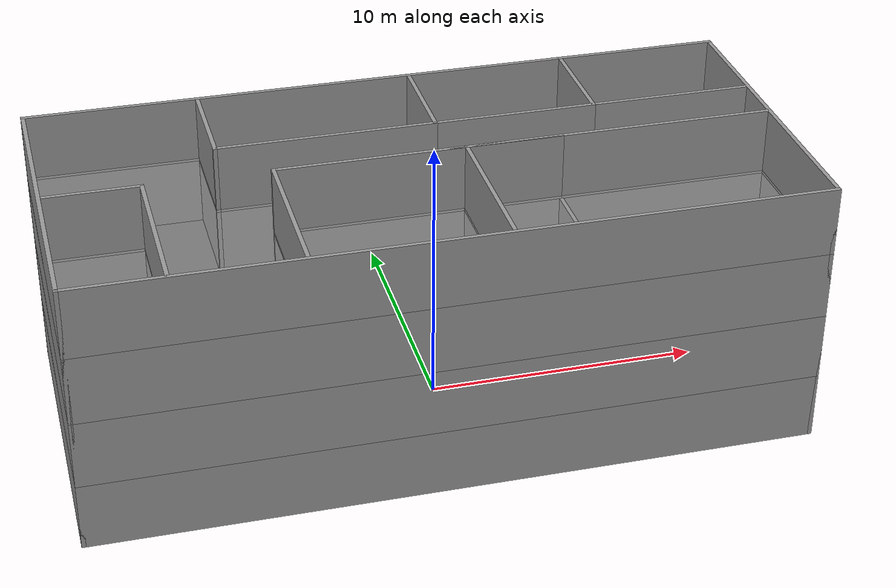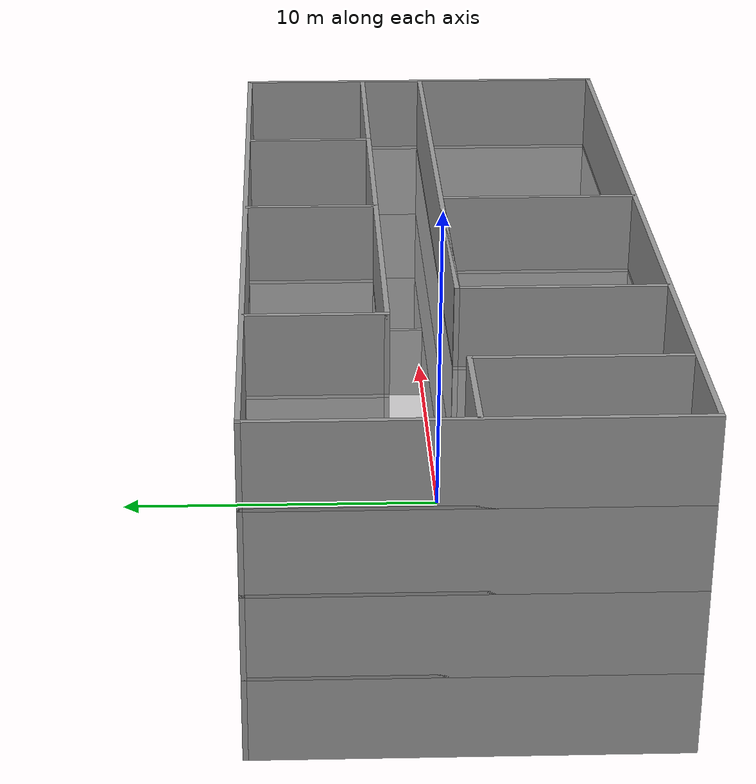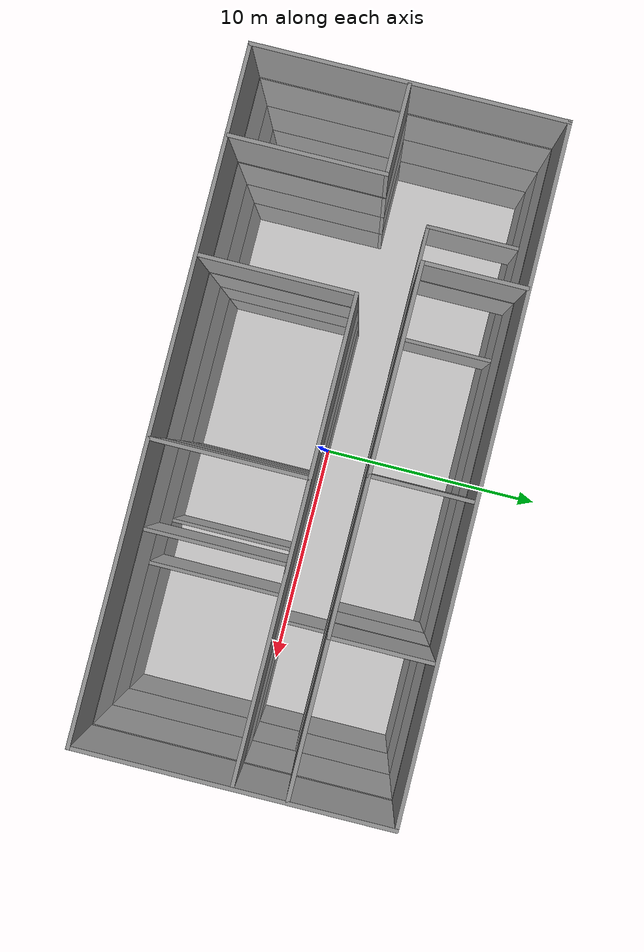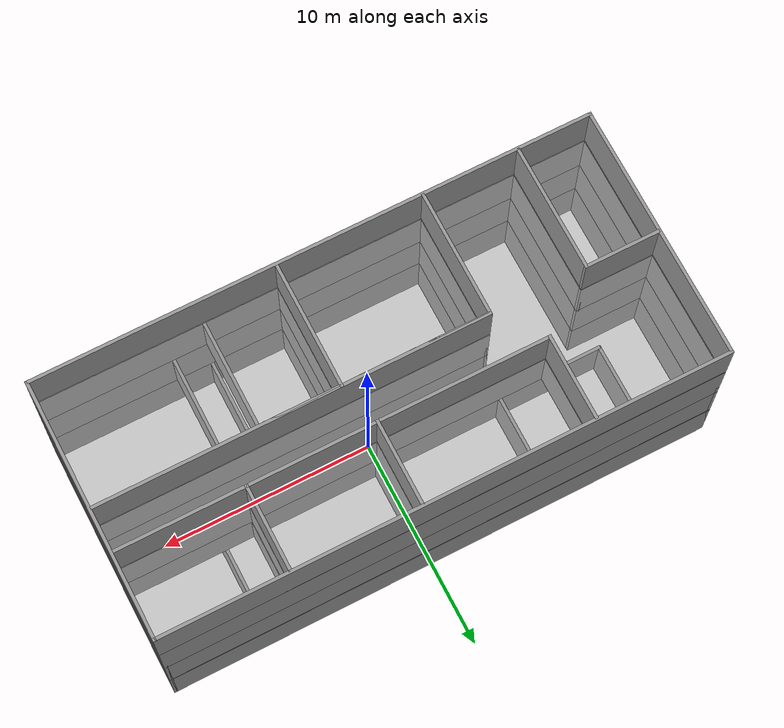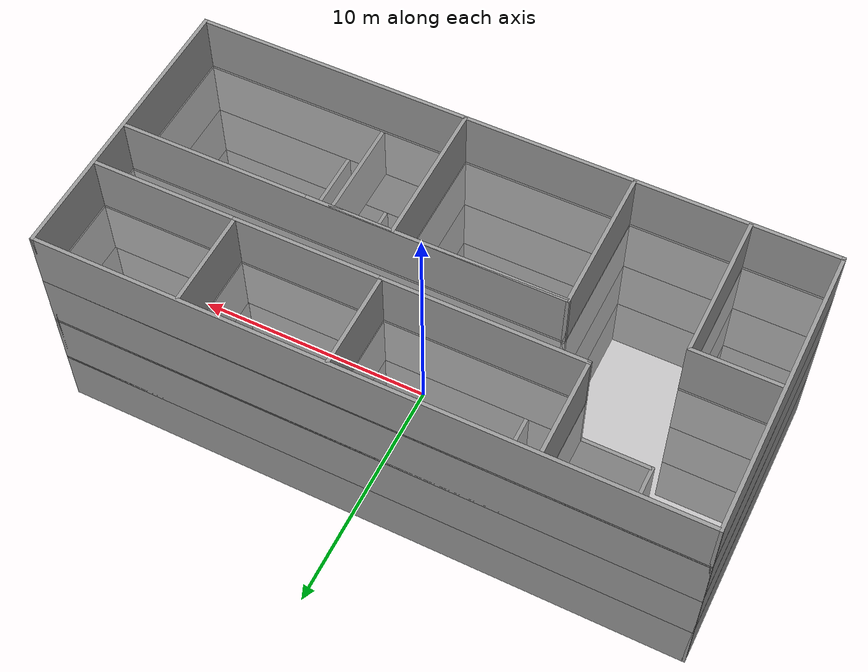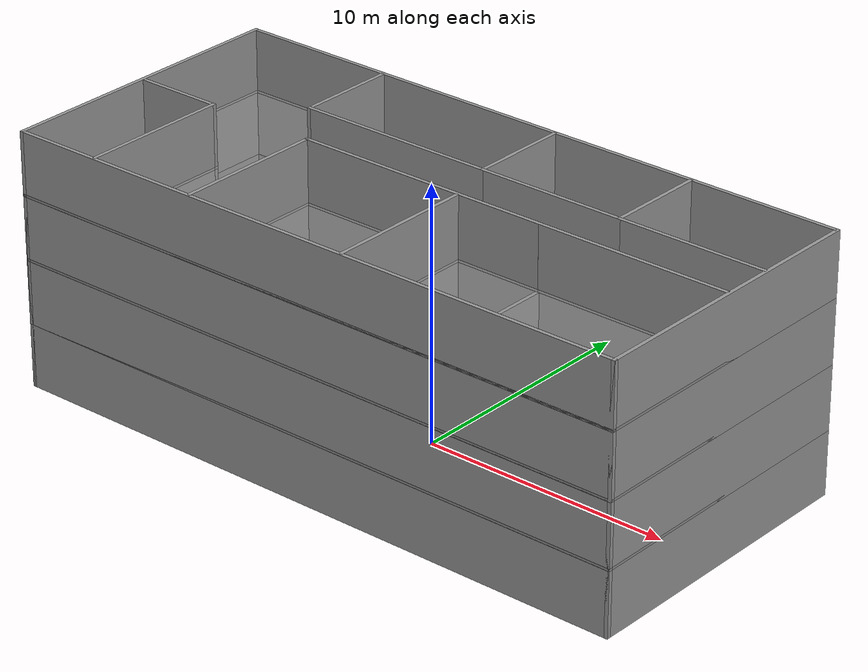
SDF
<sdf version="1.7">
 <world name="__default__">
  <gravity>0 0 -9.8</gravity>
  <magnetic_field>6e-06 2.3e-05 -4.2e-05</magnetic_field>
  <atmosphere type="adiabatic"/>
  <physics type="ode">
   <max_step_size>0.001</max_step_size>
   <real_time_factor>1</real_time_factor>
   <real_time_update_rate>1000</real_time_update_rate>
  </physics>
  <scene><ambient>0.4 0.4 0.4 1</ambient><background>0.7 0.7 0.7 1</background><shadows>1</shadows></scene>
  <spherical_coordinates>
   <surface_model>EARTH_WGS84</surface_model>
   <latitude_deg>0</latitude_deg>
   <longitude_deg>0</longitude_deg>
   <elevation>0</elevation>
   <heading_deg>0</heading_deg>
  </spherical_coordinates>
  <model name="level4_floor">
   <link name="Floor_0">
    <pose>0 0 2.5 0 -0 0</pose>
    <inertial>
     <mass>1</mass>
     <inertia><ixx>1</ixx><ixy>0</ixy><ixz>0</ixz><iyy>1</iyy><iyz>0</iyz><izz>1</izz></inertia>
    </inertial>
    <visual name="Floor_0_Visual">
     <pose>0 0 0.05 0 -0 0</pose>
     <geometry><box><size>26 12 0.1</size></box></geometry>
     <material>
      <script><uri>file://media/materials/scripts/gazebo.material</uri><name>Gazebo/Grey</name></script>
      <ambient>1 1 1 1</ambient>
      <shader type="pixel"><normal_map>__default__</normal_map></shader>
      <diffuse>0.7 0.7 0.7 1</diffuse>
      <specular>0.01 0.01 0.01 1</specular>
      <emissive>0 0 0 1</emissive>
     </material>
     <meta><layer>1</layer></meta>
     <transparency>0.5</transparency>
    </visual>
    <collision name="Floor_0_Collision">
     <pose>0 0 0.05 0 -0 0</pose>
     <geometry><box><size>26 12 0.1</size></box></geometry>
     <surface>
      <friction>
       <ode><mu>1</mu><mu2>1</mu2><fdir1>0 0 0</fdir1><slip1>0</slip1><slip2>0</slip2></ode>
       <torsional>
        <coefficient>1</coefficient>
        <patch_radius>0</patch_radius>
        <surface_radius>0</surface_radius>
        <use_patch_radius>1</use_patch_radius>
        <ode><slip>0</slip></ode>
       </torsional>
      </friction>
      <bounce><restitution_coefficient>0</restitution_coefficient><threshold>1e+06</threshold></bounce>
      <contact>
       <collide_without_contact>0</collide_without_contact>
       <collide_without_contact_bitmask>1</collide_without_contact_bitmask>
       <collide_bitmask>1</collide_bitmask>
       <ode>
        <soft_cfm>0</soft_cfm>
        <soft_erp>0.2</soft_erp>
        <kp>1e+13</kp>
        <kd>1</kd>
        <max_vel>0.01</max_vel>
        <min_depth>0</min_depth>
       </ode>
       <bullet>
        <split_impulse>1</split_impulse>
        <split_impulse_penetration_threshold>-0.01</split_impulse_penetration_threshold>
        <soft_cfm>0</soft_cfm>
        <soft_erp>0.2</soft_erp>
        <kp>1e+13</kp>
        <kd>1</kd>
       </bullet>
      </contact>
     </surface>
    </collision>
   </link>
   <link name="Floor_1">
    <pose>0 0 5 0 -0 0</pose>
    <inertial>
     <mass>1</mass>
     <inertia><ixx>1</ixx><ixy>0</ixy><ixz>0</ixz><iyy>1</iyy><iyz>0</iyz><izz>1</izz></inertia>
    </inertial>
    <visual name="Floor_1_Visual">
     <pose>0 0 0.05 0 -0 0</pose>
     <geometry><box><size>26 12 0.1</size></box></geometry>
     <material>
      <script><uri>file://media/materials/scripts/gazebo.material</uri><name>Gazebo/Grey</name></script>
      <ambient>1 1 1 1</ambient>
      <shader type="pixel"><normal_map>__default__</normal_map></shader>
      <diffuse>0.7 0.7 0.7 1</diffuse>
      <specular>0.01 0.01 0.01 1</specular>
      <emissive>0 0 0 1</emissive>
     </material>
     <meta><layer>2</layer></meta>
     <transparency>0.5</transparency>
    </visual>
    <collision name="Floor_1_Collision">
     <pose>0 0 0.05 0 -0 0</pose>
     <geometry><box><size>26 12 0.1</size></box></geometry>
     <surface>
      <friction>
       <ode><mu>1</mu><mu2>1</mu2><fdir1>0 0 0</fdir1><slip1>0</slip1><slip2>0</slip2></ode>
       <torsional>
        <coefficient>1</coefficient>
        <patch_radius>0</patch_radius>
        <surface_radius>0</surface_radius>
        <use_patch_radius>1</use_patch_radius>
        <ode><slip>0</slip></ode>
       </torsional>
      </friction>
      <bounce><restitution_coefficient>0</restitution_coefficient><threshold>1e+06</threshold></bounce>
      <contact>
       <collide_without_contact>0</collide_without_contact>
       <collide_without_contact_bitmask>1</collide_without_contact_bitmask>
       <collide_bitmask>1</collide_bitmask>
       <ode>
        <soft_cfm>0</soft_cfm>
        <soft_erp>0.2</soft_erp>
        <kp>1e+13</kp>
        <kd>1</kd>
        <max_vel>0.01</max_vel>
        <min_depth>0</min_depth>
       </ode>
       <bullet>
        <split_impulse>1</split_impulse>
        <split_impulse_penetration_threshold>-0.01</split_impulse_penetration_threshold>
        <soft_cfm>0</soft_cfm>
        <soft_erp>0.2</soft_erp>
        <kp>1e+13</kp>
        <kd>1</kd>
       </bullet>
      </contact>
     </surface>
    </collision>
   </link>
   <link name="Floor_2">
    <pose>0 0 7.5 0 -0 0</pose>
    <inertial>
     <mass>1</mass>
     <inertia><ixx>1</ixx><ixy>0</ixy><ixz>0</ixz><iyy>1</iyy><iyz>0</iyz><izz>1</izz></inertia>
    </inertial>
    <visual name="Floor_2_Visual">
     <pose>0 0 0.05 0 -0 0</pose>
     <geometry><box><size>26 12 0.1</size></box></geometry>
     <material>
      <script><uri>file://media/materials/scripts/gazebo.material</uri><name>Gazebo/Grey</name></script>
      <ambient>1 1 1 1</ambient>
      <shader type="pixel"><normal_map>__default__</normal_map></shader>
      <diffuse>0.7 0.7 0.7 1</diffuse>
      <specular>0.01 0.01 0.01 1</specular>
      <emissive>0 0 0 1</emissive>
     </material>
     <meta><layer>3</layer></meta>
     <transparency>0.5</transparency>
    </visual>
    <collision name="Floor_2_Collision">
     <pose>0 0 0.05 0 -0 0</pose>
     <geometry><box><size>26 12 0.1</size></box></geometry>
     <surface>
      <friction>
       <ode><mu>1</mu><mu2>1</mu2><fdir1>0 0 0</fdir1><slip1>0</slip1><slip2>0</slip2></ode>
       <torsional>
        <coefficient>1</coefficient>
        <patch_radius>0</patch_radius>
        <surface_radius>0</surface_radius>
        <use_patch_radius>1</use_patch_radius>
        <ode><slip>0</slip></ode>
       </torsional>
      </friction>
      <bounce><restitution_coefficient>0</restitution_coefficient><threshold>1e+06</threshold></bounce>
      <contact>
       <collide_without_contact>0</collide_without_contact>
       <collide_without_contact_bitmask>1</collide_without_contact_bitmask>
       <collide_bitmask>1</collide_bitmask>
       <ode>
        <soft_cfm>0</soft_cfm>
        <soft_erp>0.2</soft_erp>
        <kp>1e+13</kp>
        <kd>1</kd>
        <max_vel>0.01</max_vel>
        <min_depth>0</min_depth>
       </ode>
       <bullet>
        <split_impulse>1</split_impulse>
        <split_impulse_penetration_threshold>-0.01</split_impulse_penetration_threshold>
        <soft_cfm>0</soft_cfm>
        <soft_erp>0.2</soft_erp>
        <kp>1e+13</kp>
        <kd>1</kd>
       </bullet>
      </contact>
     </surface>
    </collision>
   </link>
   <link name="Wall_0">
    <pose>0 5.925 0 0 -0 0</pose>
    <visual name="Wall_0_Visual">
     <pose>0 0 1.25 0 -0 0</pose>
     <geometry><box><size>26 0.15 2.5</size></box></geometry>
     <material>
      <script><uri>file://media/materials/scripts/gazebo.material</uri><name>Gazebo/Grey</name></script>
      <ambient>1 1 1 1</ambient>
      <shader type="pixel"/>
     </material>
     <meta><layer>0</layer></meta>
    </visual>
    <collision name="Wall_0_Collision">
     <pose>0 0 1.25 0 -0 0</pose>
     <geometry><box><size>26 0.15 2.5</size></box></geometry>
     <surface>
      <friction>
       <ode><mu>1</mu><mu2>1</mu2><fdir1>0 0 0</fdir1><slip1>0</slip1><slip2>0</slip2></ode>
       <torsional>
        <coefficient>1</coefficient>
        <patch_radius>0</patch_radius>
        <surface_radius>0</surface_radius>
        <use_patch_radius>1</use_patch_radius>
        <ode><slip>0</slip></ode>
       </torsional>
      </friction>
      <bounce><restitution_coefficient>0</restitution_coefficient><threshold>1e+06</threshold></bounce>
      <contact>
       <collide_without_contact>0</collide_without_contact>
       <collide_without_contact_bitmask>1</collide_without_contact_bitmask>
       <collide_bitmask>1</collide_bitmask>
       <ode>
        <soft_cfm>0</soft_cfm>
        <soft_erp>0.2</soft_erp>
        <kp>1e+13</kp>
        <kd>1</kd>
        <max_vel>0.01</max_vel>
        <min_depth>0</min_depth>
       </ode>
       <bullet>
        <split_impulse>1</split_impulse>
        <split_impulse_penetration_threshold>-0.01</split_impulse_penetration_threshold>
        <soft_cfm>0</soft_cfm>
        <soft_erp>0.2</soft_erp>
        <kp>1e+13</kp>
        <kd>1</kd>
       </bullet>
      </contact>
     </surface>
    </collision>
   </link>
   <link name="Wall_12">
    <pose>3.88883 -0.004681 0 0 -0 0</pose>
    <visual name="Wall_12_Visual">
     <pose>0 0 1.25 0 -0 0</pose>
     <geometry><box><size>18 0.15 2.5</size></box></geometry>
     <material>
      <script><uri>file://media/materials/scripts/gazebo.material</uri><name>Gazebo/Grey</name></script>
      <ambient>1 1 1 1</ambient>
      <shader type="pixel"/>
     </material>
     <meta><layer>0</layer></meta>
    </visual>
    <collision name="Wall_12_Collision">
     <pose>0 0 1.25 0 -0 0</pose>
     <geometry><box><size>18 0.15 2.5</size></box></geometry>
     <surface>
      <friction>
       <ode><mu>1</mu><mu2>1</mu2><fdir1>0 0 0</fdir1><slip1>0</slip1><slip2>0</slip2></ode>
       <torsional>
        <coefficient>1</coefficient>
        <patch_radius>0</patch_radius>
        <surface_radius>0</surface_radius>
        <use_patch_radius>1</use_patch_radius>
        <ode><slip>0</slip></ode>
       </torsional>
      </friction>
      <bounce><restitution_coefficient>0</restitution_coefficient><threshold>1e+06</threshold></bounce>
      <contact>
       <collide_without_contact>0</collide_without_contact>
       <collide_without_contact_bitmask>1</collide_without_contact_bitmask>
       <collide_bitmask>1</collide_bitmask>
       <ode>
        <soft_cfm>0</soft_cfm>
        <soft_erp>0.2</soft_erp>
        <kp>1e+13</kp>
        <kd>1</kd>
        <max_vel>0.01</max_vel>
        <min_depth>0</min_depth>
       </ode>
       <bullet>
        <split_impulse>1</split_impulse>
        <split_impulse_penetration_threshold>-0.01</split_impulse_penetration_threshold>
        <soft_cfm>0</soft_cfm>
        <soft_erp>0.2</soft_erp>
        <kp>1e+13</kp>
        <kd>1</kd>
       </bullet>
      </contact>
     </surface>
    </collision>
   </link>
   <link name="Wall_14">
    <pose>-5.03617 -2.92968 0 0 0 -1.5708</pose>
    <visual name="Wall_14_Visual">
     <pose>0 0 1.25 0 -0 0</pose>
     <geometry><box><size>6 0.15 2.5</size></box></geometry>
     <material>
      <script><uri>file://media/materials/scripts/gazebo.material</uri><name>Gazebo/Grey</name></script>
      <ambient>1 1 1 1</ambient>
      <shader type="pixel"/>
     </material>
     <meta><layer>0</layer></meta>
    </visual>
    <collision name="Wall_14_Collision">
     <pose>0 0 1.25 0 -0 0</pose>
     <geometry><box><size>6 0.15 2.5</size></box></geometry>
     <surface>
      <friction>
       <ode><mu>1</mu><mu2>1</mu2><fdir1>0 0 0</fdir1><slip1>0</slip1><slip2>0</slip2></ode>
       <torsional>
        <coefficient>1</coefficient>
        <patch_radius>0</patch_radius>
        <surface_radius>0</surface_radius>
        <use_patch_radius>1</use_patch_radius>
        <ode><slip>0</slip></ode>
       </torsional>
      </friction>
      <bounce><restitution_coefficient>0</restitution_coefficient><threshold>1e+06</threshold></bounce>
      <contact>
       <collide_without_contact>0</collide_without_contact>
       <collide_without_contact_bitmask>1</collide_without_contact_bitmask>
       <collide_bitmask>1</collide_bitmask>
       <ode>
        <soft_cfm>0</soft_cfm>
        <soft_erp>0.2</soft_erp>
        <kp>1e+13</kp>
        <kd>1</kd>
        <max_vel>0.01</max_vel>
        <min_depth>0</min_depth>
       </ode>
       <bullet>
        <split_impulse>1</split_impulse>
        <split_impulse_penetration_threshold>-0.01</split_impulse_penetration_threshold>
        <soft_cfm>0</soft_cfm>
        <soft_erp>0.2</soft_erp>
        <kp>1e+13</kp>
        <kd>1</kd>
       </bullet>
      </contact>
     </surface>
    </collision>
   </link>
   <link name="Wall_16">
    <pose>1.74198 -2.94095 0 0 0 -1.5708</pose>
    <visual name="Wall_16_Visual">
     <pose>0 0 1.25 0 -0 0</pose>
     <geometry><box><size>6 0.15 2.5</size></box></geometry>
     <material>
      <script><uri>file://media/materials/scripts/gazebo.material</uri><name>Gazebo/Grey</name></script>
      <ambient>1 1 1 1</ambient>
      <shader type="pixel"/>
     </material>
     <meta><layer>0</layer></meta>
    </visual>
    <collision name="Wall_16_Collision">
     <pose>0 0 1.25 0 -0 0</pose>
     <geometry><box><size>6 0.15 2.5</size></box></geometry>
     <surface>
      <friction>
       <ode><mu>1</mu><mu2>1</mu2><fdir1>0 0 0</fdir1><slip1>0</slip1><slip2>0</slip2></ode>
       <torsional>
        <coefficient>1</coefficient>
        <patch_radius>0</patch_radius>
        <surface_radius>0</surface_radius>
        <use_patch_radius>1</use_patch_radius>
        <ode><slip>0</slip></ode>
       </torsional>
      </friction>
      <bounce><restitution_coefficient>0</restitution_coefficient><threshold>1e+06</threshold></bounce>
      <contact>
       <collide_without_contact>0</collide_without_contact>
       <collide_without_contact_bitmask>1</collide_without_contact_bitmask>
       <collide_bitmask>1</collide_bitmask>
       <ode>
        <soft_cfm>0</soft_cfm>
        <soft_erp>0.2</soft_erp>
        <kp>1e+13</kp>
        <kd>1</kd>
        <max_vel>0.01</max_vel>
        <min_depth>0</min_depth>
       </ode>
       <bullet>
        <split_impulse>1</split_impulse>
        <split_impulse_penetration_threshold>-0.01</split_impulse_penetration_threshold>
        <soft_cfm>0</soft_cfm>
        <soft_erp>0.2</soft_erp>
        <kp>1e+13</kp>
        <kd>1</kd>
       </bullet>
      </contact>
     </surface>
    </collision>
   </link>
   <link name="Wall_18">
    <pose>-1.68374 -0.007809 0 0 -0 0</pose>
    <visual name="Wall_18_Visual">
     <pose>0 0 1.25 0 -0 0</pose>
     <geometry><box><size>6.75 0.15 2.5</size></box></geometry>
     <material>
      <script><uri>file://media/materials/scripts/gazebo.material</uri><name>Gazebo/Grey</name></script>
      <ambient>1 1 1 1</ambient>
      <shader type="pixel"/>
     </material>
     <meta><layer>0</layer></meta>
    </visual>
    <collision name="Wall_18_Collision">
     <pose>0 0 1.25 0 -0 0</pose>
     <geometry><box><size>6.75 0.15 2.5</size></box></geometry>
     <surface>
      <friction>
       <ode><mu>1</mu><mu2>1</mu2><fdir1>0 0 0</fdir1><slip1>0</slip1><slip2>0</slip2></ode>
       <torsional>
        <coefficient>1</coefficient>
        <patch_radius>0</patch_radius>
        <surface_radius>0</surface_radius>
        <use_patch_radius>1</use_patch_radius>
        <ode><slip>0</slip></ode>
       </torsional>
      </friction>
      <bounce><restitution_coefficient>0</restitution_coefficient><threshold>1e+06</threshold></bounce>
      <contact>
       <collide_without_contact>0</collide_without_contact>
       <collide_without_contact_bitmask>1</collide_without_contact_bitmask>
       <collide_bitmask>1</collide_bitmask>
       <ode>
        <soft_cfm>0</soft_cfm>
        <soft_erp>0.2</soft_erp>
        <kp>1e+13</kp>
        <kd>1</kd>
        <max_vel>0.01</max_vel>
        <min_depth>0</min_depth>
       </ode>
       <bullet>
        <split_impulse>1</split_impulse>
        <split_impulse_penetration_threshold>-0.01</split_impulse_penetration_threshold>
        <soft_cfm>0</soft_cfm>
        <soft_erp>0.2</soft_erp>
        <kp>1e+13</kp>
        <kd>1</kd>
       </bullet>
      </contact>
     </surface>
    </collision>
   </link>
   <link name="Wall_2">
    <pose>-12.925 0 0 0 0 -1.5708</pose>
    <visual name="Wall_2_Visual">
     <pose>0 0 1.25 0 -0 0</pose>
     <geometry><box><size>12 0.15 2.5</size></box></geometry>
     <material>
      <script><uri>file://media/materials/scripts/gazebo.material</uri><name>Gazebo/Grey</name></script>
      <ambient>1 1 1 1</ambient>
      <shader type="pixel"/>
     </material>
     <meta><layer>0</layer></meta>
    </visual>
    <collision name="Wall_2_Collision">
     <pose>0 0 1.25 0 -0 0</pose>
     <geometry><box><size>12 0.15 2.5</size></box></geometry>
     <surface>
      <friction>
       <ode><mu>1</mu><mu2>1</mu2><fdir1>0 0 0</fdir1><slip1>0</slip1><slip2>0</slip2></ode>
       <torsional>
        <coefficient>1</coefficient>
        <patch_radius>0</patch_radius>
        <surface_radius>0</surface_radius>
        <use_patch_radius>1</use_patch_radius>
        <ode><slip>0</slip></ode>
       </torsional>
      </friction>
      <bounce><restitution_coefficient>0</restitution_coefficient><threshold>1e+06</threshold></bounce>
      <contact>
       <collide_without_contact>0</collide_without_contact>
       <collide_without_contact_bitmask>1</collide_without_contact_bitmask>
       <collide_bitmask>1</collide_bitmask>
       <ode>
        <soft_cfm>0</soft_cfm>
        <soft_erp>0.2</soft_erp>
        <kp>1e+13</kp>
        <kd>1</kd>
        <max_vel>0.01</max_vel>
        <min_depth>0</min_depth>
       </ode>
       <bullet>
        <split_impulse>1</split_impulse>
        <split_impulse_penetration_threshold>-0.01</split_impulse_penetration_threshold>
        <soft_cfm>0</soft_cfm>
        <soft_erp>0.2</soft_erp>
        <kp>1e+13</kp>
        <kd>1</kd>
       </bullet>
      </contact>
     </surface>
    </collision>
   </link>
   <link name="Wall_20">
    <pose>5.23395 -2.97304 0 0 0 -1.5708</pose>
    <visual name="Wall_20_Visual">
     <pose>0 0 1.25 0 -0 0</pose>
     <geometry><box><size>6 0.15 2.5</size></box></geometry>
     <material>
      <script><uri>file://media/materials/scripts/gazebo.material</uri><name>Gazebo/Grey</name></script>
      <ambient>1 1 1 1</ambient>
      <shader type="pixel"/>
     </material>
     <meta><layer>0</layer></meta>
    </visual>
    <collision name="Wall_20_Collision">
     <pose>0 0 1.25 0 -0 0</pose>
     <geometry><box><size>6 0.15 2.5</size></box></geometry>
     <surface>
      <friction>
       <ode><mu>1</mu><mu2>1</mu2><fdir1>0 0 0</fdir1><slip1>0</slip1><slip2>0</slip2></ode>
       <torsional>
        <coefficient>1</coefficient>
        <patch_radius>0</patch_radius>
        <surface_radius>0</surface_radius>
        <use_patch_radius>1</use_patch_radius>
        <ode><slip>0</slip></ode>
       </torsional>
      </friction>
      <bounce><restitution_coefficient>0</restitution_coefficient><threshold>1e+06</threshold></bounce>
      <contact>
       <collide_without_contact>0</collide_without_contact>
       <collide_without_contact_bitmask>1</collide_without_contact_bitmask>
       <collide_bitmask>1</collide_bitmask>
       <ode>
        <soft_cfm>0</soft_cfm>
        <soft_erp>0.2</soft_erp>
        <kp>1e+13</kp>
        <kd>1</kd>
        <max_vel>0.01</max_vel>
        <min_depth>0</min_depth>
       </ode>
       <bullet>
        <split_impulse>1</split_impulse>
        <split_impulse_penetration_threshold>-0.01</split_impulse_penetration_threshold>
        <soft_cfm>0</soft_cfm>
        <soft_erp>0.2</soft_erp>
        <kp>1e+13</kp>
        <kd>1</kd>
       </bullet>
      </contact>
     </surface>
    </collision>
   </link>
   <link name="Wall_22">
    <pose>3.48965 -0.007809 0 0 -0 0</pose>
    <visual name="Wall_22_Visual">
     <pose>0 0 1.25 0 -0 0</pose>
     <geometry><box><size>3.5 0.15 2.5</size></box></geometry>
     <material>
      <script><uri>file://media/materials/scripts/gazebo.material</uri><name>Gazebo/Grey</name></script>
      <ambient>1 1 1 1</ambient>
      <shader type="pixel"/>
     </material>
     <meta><layer>0</layer></meta>
    </visual>
    <collision name="Wall_22_Collision">
     <pose>0 0 1.25 0 -0 0</pose>
     <geometry><box><size>3.5 0.15 2.5</size></box></geometry>
     <surface>
      <friction>
       <ode><mu>1</mu><mu2>1</mu2><fdir1>0 0 0</fdir1><slip1>0</slip1><slip2>0</slip2></ode>
       <torsional>
        <coefficient>1</coefficient>
        <patch_radius>0</patch_radius>
        <surface_radius>0</surface_radius>
        <use_patch_radius>1</use_patch_radius>
        <ode><slip>0</slip></ode>
       </torsional>
      </friction>
      <bounce><restitution_coefficient>0</restitution_coefficient><threshold>1e+06</threshold></bounce>
      <contact>
       <collide_without_contact>0</collide_without_contact>
       <collide_without_contact_bitmask>1</collide_without_contact_bitmask>
       <collide_bitmask>1</collide_bitmask>
       <ode>
        <soft_cfm>0</soft_cfm>
        <soft_erp>0.2</soft_erp>
        <kp>1e+13</kp>
        <kd>1</kd>
        <max_vel>0.01</max_vel>
        <min_depth>0</min_depth>
       </ode>
       <bullet>
        <split_impulse>1</split_impulse>
        <split_impulse_penetration_threshold>-0.01</split_impulse_penetration_threshold>
        <soft_cfm>0</soft_cfm>
        <soft_erp>0.2</soft_erp>
        <kp>1e+13</kp>
        <kd>1</kd>
       </bullet>
      </contact>
     </surface>
    </collision>
   </link>
   <link name="Wall_24">
    <pose>8.37715 2.92436 0 0 -0 1.5708</pose>
    <visual name="Wall_24_Visual">
     <pose>0 0 1.25 0 -0 0</pose>
     <geometry><box><size>6 0.15 2.5</size></box></geometry>
     <material>
      <script><uri>file://media/materials/scripts/gazebo.material</uri><name>Gazebo/Grey</name></script>
      <ambient>1 1 1 1</ambient>
      <shader type="pixel"/>
     </material>
     <meta><layer>0</layer></meta>
    </visual>
    <collision name="Wall_24_Collision">
     <pose>0 0 1.25 0 -0 0</pose>
     <geometry><box><size>6 0.15 2.5</size></box></geometry>
     <surface>
      <friction>
       <ode><mu>1</mu><mu2>1</mu2><fdir1>0 0 0</fdir1><slip1>0</slip1><slip2>0</slip2></ode>
       <torsional>
        <coefficient>1</coefficient>
        <patch_radius>0</patch_radius>
        <surface_radius>0</surface_radius>
        <use_patch_radius>1</use_patch_radius>
        <ode><slip>0</slip></ode>
       </torsional>
      </friction>
      <bounce><restitution_coefficient>0</restitution_coefficient><threshold>1e+06</threshold></bounce>
      <contact>
       <collide_without_contact>0</collide_without_contact>
       <collide_without_contact_bitmask>1</collide_without_contact_bitmask>
       <collide_bitmask>1</collide_bitmask>
       <ode>
        <soft_cfm>0</soft_cfm>
        <soft_erp>0.2</soft_erp>
        <kp>1e+13</kp>
        <kd>1</kd>
        <max_vel>0.01</max_vel>
        <min_depth>0</min_depth>
       </ode>
       <bullet>
        <split_impulse>1</split_impulse>
        <split_impulse_penetration_threshold>-0.01</split_impulse_penetration_threshold>
        <soft_cfm>0</soft_cfm>
        <soft_erp>0.2</soft_erp>
        <kp>1e+13</kp>
        <kd>1</kd>
       </bullet>
      </contact>
     </surface>
    </collision>
   </link>
   <link name="Wall_26">
    <pose>-11.1664 -0.004708 0 0 -0 0</pose>
    <visual name="Wall_26_Visual">
     <pose>0 0 1.25 0 -0 0</pose>
     <geometry><box><size>3.5 0.15 2.5</size></box></geometry>
     <material>
      <script><uri>file://media/materials/scripts/gazebo.material</uri><name>Gazebo/Grey</name></script>
      <ambient>1 1 1 1</ambient>
      <shader type="pixel"/>
     </material>
     <meta><layer>0</layer></meta>
    </visual>
    <collision name="Wall_26_Collision">
     <pose>0 0 1.25 0 -0 0</pose>
     <geometry><box><size>3.5 0.15 2.5</size></box></geometry>
     <surface>
      <friction>
       <ode><mu>1</mu><mu2>1</mu2><fdir1>0 0 0</fdir1><slip1>0</slip1><slip2>0</slip2></ode>
       <torsional>
        <coefficient>1</coefficient>
        <patch_radius>0</patch_radius>
        <surface_radius>0</surface_radius>
        <use_patch_radius>1</use_patch_radius>
        <ode><slip>0</slip></ode>
       </torsional>
      </friction>
      <bounce><restitution_coefficient>0</restitution_coefficient><threshold>1e+06</threshold></bounce>
      <contact>
       <collide_without_contact>0</collide_without_contact>
       <collide_without_contact_bitmask>1</collide_without_contact_bitmask>
       <collide_bitmask>1</collide_bitmask>
       <ode>
        <soft_cfm>0</soft_cfm>
        <soft_erp>0.2</soft_erp>
        <kp>1e+13</kp>
        <kd>1</kd>
        <max_vel>0.01</max_vel>
        <min_depth>0</min_depth>
       </ode>
       <bullet>
        <split_impulse>1</split_impulse>
        <split_impulse_penetration_threshold>-0.01</split_impulse_penetration_threshold>
        <soft_cfm>0</soft_cfm>
        <soft_erp>0.2</soft_erp>
        <kp>1e+13</kp>
        <kd>1</kd>
       </bullet>
      </contact>
     </surface>
    </collision>
   </link>
   <link name="Wall_27">
    <pose>-9.49144 -2.92971 0 0 0 -1.5708</pose>
    <visual name="Wall_27_Visual">
     <pose>0 0 1.25 0 -0 0</pose>
     <geometry><box><size>6 0.15 2.5</size></box></geometry>
     <material>
      <script><uri>file://media/materials/scripts/gazebo.material</uri><name>Gazebo/Grey</name></script>
      <ambient>1 1 1 1</ambient>
      <shader type="pixel"/>
     </material>
     <meta><layer>0</layer></meta>
    </visual>
    <collision name="Wall_27_Collision">
     <pose>0 0 1.25 0 -0 0</pose>
     <geometry><box><size>6 0.15 2.5</size></box></geometry>
     <surface>
      <friction>
       <ode><mu>1</mu><mu2>1</mu2><fdir1>0 0 0</fdir1><slip1>0</slip1><slip2>0</slip2></ode>
       <torsional>
        <coefficient>1</coefficient>
        <patch_radius>0</patch_radius>
        <surface_radius>0</surface_radius>
        <use_patch_radius>1</use_patch_radius>
        <ode><slip>0</slip></ode>
       </torsional>
      </friction>
      <bounce><restitution_coefficient>0</restitution_coefficient><threshold>1e+06</threshold></bounce>
      <contact>
       <collide_without_contact>0</collide_without_contact>
       <collide_without_contact_bitmask>1</collide_without_contact_bitmask>
       <collide_bitmask>1</collide_bitmask>
       <ode>
        <soft_cfm>0</soft_cfm>
        <soft_erp>0.2</soft_erp>
        <kp>1e+13</kp>
        <kd>1</kd>
        <max_vel>0.01</max_vel>
        <min_depth>0</min_depth>
       </ode>
       <bullet>
        <split_impulse>1</split_impulse>
        <split_impulse_penetration_threshold>-0.01</split_impulse_penetration_threshold>
        <soft_cfm>0</soft_cfm>
        <soft_erp>0.2</soft_erp>
        <kp>1e+13</kp>
        <kd>1</kd>
       </bullet>
      </contact>
     </surface>
    </collision>
   </link>
   <link name="Wall_29">
    <pose>0 5.925 2.5 0 -0 0</pose>
    <visual name="Wall_29_Visual">
     <pose>0 0 1.25 0 -0 0</pose>
     <geometry><box><size>26 0.15 2.5</size></box></geometry>
     <material>
      <script><uri>file://media/materials/scripts/gazebo.material</uri><name>Gazebo/Grey</name></script>
      <ambient>1 1 1 1</ambient>
      <shader type="pixel"/>
     </material>
     <meta><layer>1</layer></meta>
    </visual>
    <collision name="Wall_29_Collision">
     <pose>0 0 1.25 0 -0 0</pose>
     <geometry><box><size>26 0.15 2.5</size></box></geometry>
     <surface>
      <friction>
       <ode><mu>1</mu><mu2>1</mu2><fdir1>0 0 0</fdir1><slip1>0</slip1><slip2>0</slip2></ode>
       <torsional>
        <coefficient>1</coefficient>
        <patch_radius>0</patch_radius>
        <surface_radius>0</surface_radius>
        <use_patch_radius>1</use_patch_radius>
        <ode><slip>0</slip></ode>
       </torsional>
      </friction>
      <bounce><restitution_coefficient>0</restitution_coefficient><threshold>1e+06</threshold></bounce>
      <contact>
       <collide_without_contact>0</collide_without_contact>
       <collide_without_contact_bitmask>1</collide_without_contact_bitmask>
       <collide_bitmask>1</collide_bitmask>
       <ode>
        <soft_cfm>0</soft_cfm>
        <soft_erp>0.2</soft_erp>
        <kp>1e+13</kp>
        <kd>1</kd>
        <max_vel>0.01</max_vel>
        <min_depth>0</min_depth>
       </ode>
       <bullet>
        <split_impulse>1</split_impulse>
        <split_impulse_penetration_threshold>-0.01</split_impulse_penetration_threshold>
        <soft_cfm>0</soft_cfm>
        <soft_erp>0.2</soft_erp>
        <kp>1e+13</kp>
        <kd>1</kd>
       </bullet>
      </contact>
     </surface>
    </collision>
   </link>
   <link name="Wall_30">
    <pose>-12.925 0 2.5 0 0 -1.5708</pose>
    <visual name="Wall_30_Visual">
     <pose>0 0 1.25 0 -0 0</pose>
     <geometry><box><size>12 0.15 2.5</size></box></geometry>
     <material>
      <script><uri>file://media/materials/scripts/gazebo.material</uri><name>Gazebo/Grey</name></script>
      <ambient>1 1 1 1</ambient>
      <shader type="pixel"/>
     </material>
     <meta><layer>1</layer></meta>
    </visual>
    <collision name="Wall_30_Collision">
     <pose>0 0 1.25 0 -0 0</pose>
     <geometry><box><size>12 0.15 2.5</size></box></geometry>
     <surface>
      <friction>
       <ode><mu>1</mu><mu2>1</mu2><fdir1>0 0 0</fdir1><slip1>0</slip1><slip2>0</slip2></ode>
       <torsional>
        <coefficient>1</coefficient>
        <patch_radius>0</patch_radius>
        <surface_radius>0</surface_radius>
        <use_patch_radius>1</use_patch_radius>
        <ode><slip>0</slip></ode>
       </torsional>
      </friction>
      <bounce><restitution_coefficient>0</restitution_coefficient><threshold>1e+06</threshold></bounce>
      <contact>
       <collide_without_contact>0</collide_without_contact>
       <collide_without_contact_bitmask>1</collide_without_contact_bitmask>
       <collide_bitmask>1</collide_bitmask>
       <ode>
        <soft_cfm>0</soft_cfm>
        <soft_erp>0.2</soft_erp>
        <kp>1e+13</kp>
        <kd>1</kd>
        <max_vel>0.01</max_vel>
        <min_depth>0</min_depth>
       </ode>
       <bullet>
        <split_impulse>1</split_impulse>
        <split_impulse_penetration_threshold>-0.01</split_impulse_penetration_threshold>
        <soft_cfm>0</soft_cfm>
        <soft_erp>0.2</soft_erp>
        <kp>1e+13</kp>
        <kd>1</kd>
       </bullet>
      </contact>
     </surface>
    </collision>
   </link>
   <link name="Wall_31">
    <pose>0 -5.925 2.5 0 -0 0</pose>
    <visual name="Wall_31_Visual">
     <pose>0 0 1.25 0 -0 0</pose>
     <geometry><box><size>26 0.15 2.5</size></box></geometry>
     <material>
      <script><uri>file://media/materials/scripts/gazebo.material</uri><name>Gazebo/Grey</name></script>
      <ambient>1 1 1 1</ambient>
      <shader type="pixel"/>
     </material>
     <meta><layer>1</layer></meta>
    </visual>
    <collision name="Wall_31_Collision">
     <pose>0 0 1.25 0 -0 0</pose>
     <geometry><box><size>26 0.15 2.5</size></box></geometry>
     <surface>
      <friction>
       <ode><mu>1</mu><mu2>1</mu2><fdir1>0 0 0</fdir1><slip1>0</slip1><slip2>0</slip2></ode>
       <torsional>
        <coefficient>1</coefficient>
        <patch_radius>0</patch_radius>
        <surface_radius>0</surface_radius>
        <use_patch_radius>1</use_patch_radius>
        <ode><slip>0</slip></ode>
       </torsional>
      </friction>
      <bounce><restitution_coefficient>0</restitution_coefficient><threshold>1e+06</threshold></bounce>
      <contact>
       <collide_without_contact>0</collide_without_contact>
       <collide_without_contact_bitmask>1</collide_without_contact_bitmask>
       <collide_bitmask>1</collide_bitmask>
       <ode>
        <soft_cfm>0</soft_cfm>
        <soft_erp>0.2</soft_erp>
        <kp>1e+13</kp>
        <kd>1</kd>
        <max_vel>0.01</max_vel>
        <min_depth>0</min_depth>
       </ode>
       <bullet>
        <split_impulse>1</split_impulse>
        <split_impulse_penetration_threshold>-0.01</split_impulse_penetration_threshold>
        <soft_cfm>0</soft_cfm>
        <soft_erp>0.2</soft_erp>
        <kp>1e+13</kp>
        <kd>1</kd>
       </bullet>
      </contact>
     </surface>
    </collision>
   </link>
   <link name="Wall_32">
    <pose>12.925 0 2.5 0 0 -1.5708</pose>
    <visual name="Wall_32_Visual">
     <pose>0 0 1.25 0 -0 0</pose>
     <geometry><box><size>12 0.15 2.5</size></box></geometry>
     <material>
      <script><uri>file://media/materials/scripts/gazebo.material</uri><name>Gazebo/Grey</name></script>
      <ambient>1 1 1 1</ambient>
      <shader type="pixel"/>
     </material>
     <meta><layer>1</layer></meta>
    </visual>
    <collision name="Wall_32_Collision">
     <pose>0 0 1.25 0 -0 0</pose>
     <geometry><box><size>12 0.15 2.5</size></box></geometry>
     <surface>
      <friction>
       <ode><mu>1</mu><mu2>1</mu2><fdir1>0 0 0</fdir1><slip1>0</slip1><slip2>0</slip2></ode>
       <torsional>
        <coefficient>1</coefficient>
        <patch_radius>0</patch_radius>
        <surface_radius>0</surface_radius>
        <use_patch_radius>1</use_patch_radius>
        <ode><slip>0</slip></ode>
       </torsional>
      </friction>
      <bounce><restitution_coefficient>0</restitution_coefficient><threshold>1e+06</threshold></bounce>
      <contact>
       <collide_without_contact>0</collide_without_contact>
       <collide_without_contact_bitmask>1</collide_without_contact_bitmask>
       <collide_bitmask>1</collide_bitmask>
       <ode>
        <soft_cfm>0</soft_cfm>
        <soft_erp>0.2</soft_erp>
        <kp>1e+13</kp>
        <kd>1</kd>
        <max_vel>0.01</max_vel>
        <min_depth>0</min_depth>
       </ode>
       <bullet>
        <split_impulse>1</split_impulse>
        <split_impulse_penetration_threshold>-0.01</split_impulse_penetration_threshold>
        <soft_cfm>0</soft_cfm>
        <soft_erp>0.2</soft_erp>
        <kp>1e+13</kp>
        <kd>1</kd>
       </bullet>
      </contact>
     </surface>
    </collision>
   </link>
   <link name="Wall_33">
    <pose>3.88883 -0.004681 2.5 0 -0 0</pose>
    <visual name="Wall_33_Visual">
     <pose>0 0 1.25 0 -0 0</pose>
     <geometry><box><size>18 0.15 2.5</size></box></geometry>
     <material>
      <script><uri>file://media/materials/scripts/gazebo.material</uri><name>Gazebo/Grey</name></script>
      <ambient>1 1 1 1</ambient>
      <shader type="pixel"/>
     </material>
     <meta><layer>1</layer></meta>
    </visual>
    <collision name="Wall_33_Collision">
     <pose>0 0 1.25 0 -0 0</pose>
     <geometry><box><size>18 0.15 2.5</size></box></geometry>
     <surface>
      <friction>
       <ode><mu>1</mu><mu2>1</mu2><fdir1>0 0 0</fdir1><slip1>0</slip1><slip2>0</slip2></ode>
       <torsional>
        <coefficient>1</coefficient>
        <patch_radius>0</patch_radius>
        <surface_radius>0</surface_radius>
        <use_patch_radius>1</use_patch_radius>
        <ode><slip>0</slip></ode>
       </torsional>
      </friction>
      <bounce><restitution_coefficient>0</restitution_coefficient><threshold>1e+06</threshold></bounce>
      <contact>
       <collide_without_contact>0</collide_without_contact>
       <collide_without_contact_bitmask>1</collide_without_contact_bitmask>
       <collide_bitmask>1</collide_bitmask>
       <ode>
        <soft_cfm>0</soft_cfm>
        <soft_erp>0.2</soft_erp>
        <kp>1e+13</kp>
        <kd>1</kd>
        <max_vel>0.01</max_vel>
        <min_depth>0</min_depth>
       </ode>
       <bullet>
        <split_impulse>1</split_impulse>
        <split_impulse_penetration_threshold>-0.01</split_impulse_penetration_threshold>
        <soft_cfm>0</soft_cfm>
        <soft_erp>0.2</soft_erp>
        <kp>1e+13</kp>
        <kd>1</kd>
       </bullet>
      </contact>
     </surface>
    </collision>
   </link>
   <link name="Wall_34">
    <pose>-5.03617 -2.92968 2.5 0 0 -1.5708</pose>
    <visual name="Wall_34_Visual">
     <pose>0 0 1.25 0 -0 0</pose>
     <geometry><box><size>6 0.15 2.5</size></box></geometry>
     <material>
      <script><uri>file://media/materials/scripts/gazebo.material</uri><name>Gazebo/Grey</name></script>
      <ambient>1 1 1 1</ambient>
      <shader type="pixel"/>
     </material>
     <meta><layer>1</layer></meta>
    </visual>
    <collision name="Wall_34_Collision">
     <pose>0 0 1.25 0 -0 0</pose>
     <geometry><box><size>6 0.15 2.5</size></box></geometry>
     <surface>
      <friction>
       <ode><mu>1</mu><mu2>1</mu2><fdir1>0 0 0</fdir1><slip1>0</slip1><slip2>0</slip2></ode>
       <torsional>
        <coefficient>1</coefficient>
        <patch_radius>0</patch_radius>
        <surface_radius>0</surface_radius>
        <use_patch_radius>1</use_patch_radius>
        <ode><slip>0</slip></ode>
       </torsional>
      </friction>
      <bounce><restitution_coefficient>0</restitution_coefficient><threshold>1e+06</threshold></bounce>
      <contact>
       <collide_without_contact>0</collide_without_contact>
       <collide_without_contact_bitmask>1</collide_without_contact_bitmask>
       <collide_bitmask>1</collide_bitmask>
       <ode>
        <soft_cfm>0</soft_cfm>
        <soft_erp>0.2</soft_erp>
        <kp>1e+13</kp>
        <kd>1</kd>
        <max_vel>0.01</max_vel>
        <min_depth>0</min_depth>
       </ode>
       <bullet>
        <split_impulse>1</split_impulse>
        <split_impulse_penetration_threshold>-0.01</split_impulse_penetration_threshold>
        <soft_cfm>0</soft_cfm>
        <soft_erp>0.2</soft_erp>
        <kp>1e+13</kp>
        <kd>1</kd>
       </bullet>
      </contact>
     </surface>
    </collision>
   </link>
   <link name="Wall_35">
    <pose>1.74198 -2.94095 2.5 0 0 -1.5708</pose>
    <visual name="Wall_35_Visual">
     <pose>0 0 1.25 0 -0 0</pose>
     <geometry><box><size>6 0.15 2.5</size></box></geometry>
     <material>
      <script><uri>file://media/materials/scripts/gazebo.material</uri><name>Gazebo/Grey</name></script>
      <ambient>1 1 1 1</ambient>
      <shader type="pixel"/>
     </material>
     <meta><layer>1</layer></meta>
    </visual>
    <collision name="Wall_35_Collision">
     <pose>0 0 1.25 0 -0 0</pose>
     <geometry><box><size>6 0.15 2.5</size></box></geometry>
     <surface>
      <friction>
       <ode><mu>1</mu><mu2>1</mu2><fdir1>0 0 0</fdir1><slip1>0</slip1><slip2>0</slip2></ode>
       <torsional>
        <coefficient>1</coefficient>
        <patch_radius>0</patch_radius>
        <surface_radius>0</surface_radius>
        <use_patch_radius>1</use_patch_radius>
        <ode><slip>0</slip></ode>
       </torsional>
      </friction>
      <bounce><restitution_coefficient>0</restitution_coefficient><threshold>1e+06</threshold></bounce>
      <contact>
       <collide_without_contact>0</collide_without_contact>
       <collide_without_contact_bitmask>1</collide_without_contact_bitmask>
       <collide_bitmask>1</collide_bitmask>
       <ode>
        <soft_cfm>0</soft_cfm>
        <soft_erp>0.2</soft_erp>
        <kp>1e+13</kp>
        <kd>1</kd>
        <max_vel>0.01</max_vel>
        <min_depth>0</min_depth>
       </ode>
       <bullet>
        <split_impulse>1</split_impulse>
        <split_impulse_penetration_threshold>-0.01</split_impulse_penetration_threshold>
        <soft_cfm>0</soft_cfm>
        <soft_erp>0.2</soft_erp>
        <kp>1e+13</kp>
        <kd>1</kd>
       </bullet>
      </contact>
     </surface>
    </collision>
   </link>
   <link name="Wall_36">
    <pose>-1.68374 -0.007809 2.5 0 -0 0</pose>
    <visual name="Wall_36_Visual">
     <pose>0 0 1.25 0 -0 0</pose>
     <geometry><box><size>6.75 0.15 2.5</size></box></geometry>
     <material>
      <script><uri>file://media/materials/scripts/gazebo.material</uri><name>Gazebo/Grey</name></script>
      <ambient>1 1 1 1</ambient>
      <shader type="pixel"/>
     </material>
     <meta><layer>1</layer></meta>
    </visual>
    <collision name="Wall_36_Collision">
     <pose>0 0 1.25 0 -0 0</pose>
     <geometry><box><size>6.75 0.15 2.5</size></box></geometry>
     <surface>
      <friction>
       <ode><mu>1</mu><mu2>1</mu2><fdir1>0 0 0</fdir1><slip1>0</slip1><slip2>0</slip2></ode>
       <torsional>
        <coefficient>1</coefficient>
        <patch_radius>0</patch_radius>
        <surface_radius>0</surface_radius>
        <use_patch_radius>1</use_patch_radius>
        <ode><slip>0</slip></ode>
       </torsional>
      </friction>
      <bounce><restitution_coefficient>0</restitution_coefficient><threshold>1e+06</threshold></bounce>
      <contact>
       <collide_without_contact>0</collide_without_contact>
       <collide_without_contact_bitmask>1</collide_without_contact_bitmask>
       <collide_bitmask>1</collide_bitmask>
       <ode>
        <soft_cfm>0</soft_cfm>
        <soft_erp>0.2</soft_erp>
        <kp>1e+13</kp>
        <kd>1</kd>
        <max_vel>0.01</max_vel>
        <min_depth>0</min_depth>
       </ode>
       <bullet>
        <split_impulse>1</split_impulse>
        <split_impulse_penetration_threshold>-0.01</split_impulse_penetration_threshold>
        <soft_cfm>0</soft_cfm>
        <soft_erp>0.2</soft_erp>
        <kp>1e+13</kp>
        <kd>1</kd>
       </bullet>
      </contact>
     </surface>
    </collision>
   </link>
   <link name="Wall_37">
    <pose>6.86229 -2.97304 2.5 0 0 -1.5708</pose>
    <visual name="Wall_37_Visual">
     <pose>0 0 1.25 0 -0 0</pose>
     <geometry><box><size>6 0.15 2.5</size></box></geometry>
     <material>
      <script><uri>file://media/materials/scripts/gazebo.material</uri><name>Gazebo/Grey</name></script>
      <ambient>1 1 1 1</ambient>
      <shader type="pixel"/>
     </material>
     <meta><layer>1</layer></meta>
    </visual>
    <collision name="Wall_37_Collision">
     <pose>0 0 1.25 0 -0 0</pose>
     <geometry><box><size>6 0.15 2.5</size></box></geometry>
     <surface>
      <friction>
       <ode><mu>1</mu><mu2>1</mu2><fdir1>0 0 0</fdir1><slip1>0</slip1><slip2>0</slip2></ode>
       <torsional>
        <coefficient>1</coefficient>
        <patch_radius>0</patch_radius>
        <surface_radius>0</surface_radius>
        <use_patch_radius>1</use_patch_radius>
        <ode><slip>0</slip></ode>
       </torsional>
      </friction>
      <bounce><restitution_coefficient>0</restitution_coefficient><threshold>1e+06</threshold></bounce>
      <contact>
       <collide_without_contact>0</collide_without_contact>
       <collide_without_contact_bitmask>1</collide_without_contact_bitmask>
       <collide_bitmask>1</collide_bitmask>
       <ode>
        <soft_cfm>0</soft_cfm>
        <soft_erp>0.2</soft_erp>
        <kp>1e+13</kp>
        <kd>1</kd>
        <max_vel>0.01</max_vel>
        <min_depth>0</min_depth>
       </ode>
       <bullet>
        <split_impulse>1</split_impulse>
        <split_impulse_penetration_threshold>-0.01</split_impulse_penetration_threshold>
        <soft_cfm>0</soft_cfm>
        <soft_erp>0.2</soft_erp>
        <kp>1e+13</kp>
        <kd>1</kd>
       </bullet>
      </contact>
     </surface>
    </collision>
   </link>
   <link name="Wall_38">
    <pose>4.23965 -0.007809 2.5 0 -0 0</pose>
    <visual name="Wall_38_Visual">
     <pose>0 0 1.25 0 -0 0</pose>
     <geometry><box><size>5 0.15 2.5</size></box></geometry>
     <material>
      <script><uri>file://media/materials/scripts/gazebo.material</uri><name>Gazebo/Grey</name></script>
      <ambient>1 1 1 1</ambient>
      <shader type="pixel"/>
     </material>
     <meta><layer>1</layer></meta>
    </visual>
    <collision name="Wall_38_Collision">
     <pose>0 0 1.25 0 -0 0</pose>
     <geometry><box><size>5 0.15 2.5</size></box></geometry>
     <surface>
      <friction>
       <ode><mu>1</mu><mu2>1</mu2><fdir1>0 0 0</fdir1><slip1>0</slip1><slip2>0</slip2></ode>
       <torsional>
        <coefficient>1</coefficient>
        <patch_radius>0</patch_radius>
        <surface_radius>0</surface_radius>
        <use_patch_radius>1</use_patch_radius>
        <ode><slip>0</slip></ode>
       </torsional>
      </friction>
      <bounce><restitution_coefficient>0</restitution_coefficient><threshold>1e+06</threshold></bounce>
      <contact>
       <collide_without_contact>0</collide_without_contact>
       <collide_without_contact_bitmask>1</collide_without_contact_bitmask>
       <collide_bitmask>1</collide_bitmask>
       <ode>
        <soft_cfm>0</soft_cfm>
        <soft_erp>0.2</soft_erp>
        <kp>1e+13</kp>
        <kd>1</kd>
        <max_vel>0.01</max_vel>
        <min_depth>0</min_depth>
       </ode>
       <bullet>
        <split_impulse>1</split_impulse>
        <split_impulse_penetration_threshold>-0.01</split_impulse_penetration_threshold>
        <soft_cfm>0</soft_cfm>
        <soft_erp>0.2</soft_erp>
        <kp>1e+13</kp>
        <kd>1</kd>
       </bullet>
      </contact>
     </surface>
    </collision>
   </link>
   <link name="Wall_39">
    <pose>7.01245 3.8781 2.5 0 -0 1.5708</pose>
    <visual name="Wall_39_Visual">
     <pose>0 0 1.25 0 -0 0</pose>
     <geometry><box><size>4 0.15 2.5</size></box></geometry>
     <material>
      <script><uri>file://media/materials/scripts/gazebo.material</uri><name>Gazebo/Grey</name></script>
      <ambient>1 1 1 1</ambient>
      <shader type="pixel"/>
     </material>
     <meta><layer>1</layer></meta>
    </visual>
    <collision name="Wall_39_Collision">
     <pose>0 0 1.25 0 -0 0</pose>
     <geometry><box><size>4 0.15 2.5</size></box></geometry>
     <surface>
      <friction>
       <ode><mu>1</mu><mu2>1</mu2><fdir1>0 0 0</fdir1><slip1>0</slip1><slip2>0</slip2></ode>
       <torsional>
        <coefficient>1</coefficient>
        <patch_radius>0</patch_radius>
        <surface_radius>0</surface_radius>
        <use_patch_radius>1</use_patch_radius>
        <ode><slip>0</slip></ode>
       </torsional>
      </friction>
      <bounce><restitution_coefficient>0</restitution_coefficient><threshold>1e+06</threshold></bounce>
      <contact>
       <collide_without_contact>0</collide_without_contact>
       <collide_without_contact_bitmask>1</collide_without_contact_bitmask>
       <collide_bitmask>1</collide_bitmask>
       <ode>
        <soft_cfm>0</soft_cfm>
        <soft_erp>0.2</soft_erp>
        <kp>1e+13</kp>
        <kd>1</kd>
        <max_vel>0.01</max_vel>
        <min_depth>0</min_depth>
       </ode>
       <bullet>
        <split_impulse>1</split_impulse>
        <split_impulse_penetration_threshold>-0.01</split_impulse_penetration_threshold>
        <soft_cfm>0</soft_cfm>
        <soft_erp>0.2</soft_erp>
        <kp>1e+13</kp>
        <kd>1</kd>
       </bullet>
      </contact>
     </surface>
    </collision>
   </link>
   <link name="Wall_40">
    <pose>-11.1664 -0.004708 2.5 0 -0 0</pose>
    <visual name="Wall_40_Visual">
     <pose>0 0 1.25 0 -0 0</pose>
     <geometry><box><size>3.5 0.15 2.5</size></box></geometry>
     <material>
      <script><uri>file://media/materials/scripts/gazebo.material</uri><name>Gazebo/Grey</name></script>
      <ambient>1 1 1 1</ambient>
      <shader type="pixel"/>
     </material>
     <meta><layer>1</layer></meta>
    </visual>
    <collision name="Wall_40_Collision">
     <pose>0 0 1.25 0 -0 0</pose>
     <geometry><box><size>3.5 0.15 2.5</size></box></geometry>
     <surface>
      <friction>
       <ode><mu>1</mu><mu2>1</mu2><fdir1>0 0 0</fdir1><slip1>0</slip1><slip2>0</slip2></ode>
       <torsional>
        <coefficient>1</coefficient>
        <patch_radius>0</patch_radius>
        <surface_radius>0</surface_radius>
        <use_patch_radius>1</use_patch_radius>
        <ode><slip>0</slip></ode>
       </torsional>
      </friction>
      <bounce><restitution_coefficient>0</restitution_coefficient><threshold>1e+06</threshold></bounce>
      <contact>
       <collide_without_contact>0</collide_without_contact>
       <collide_without_contact_bitmask>1</collide_without_contact_bitmask>
       <collide_bitmask>1</collide_bitmask>
       <ode>
        <soft_cfm>0</soft_cfm>
        <soft_erp>0.2</soft_erp>
        <kp>1e+13</kp>
        <kd>1</kd>
        <max_vel>0.01</max_vel>
        <min_depth>0</min_depth>
       </ode>
       <bullet>
        <split_impulse>1</split_impulse>
        <split_impulse_penetration_threshold>-0.01</split_impulse_penetration_threshold>
        <soft_cfm>0</soft_cfm>
        <soft_erp>0.2</soft_erp>
        <kp>1e+13</kp>
        <kd>1</kd>
       </bullet>
      </contact>
     </surface>
    </collision>
   </link>
   <link name="Wall_41">
    <pose>-9.49144 -2.92971 2.5 0 0 -1.5708</pose>
    <visual name="Wall_41_Visual">
     <pose>0 0 1.25 0 -0 0</pose>
     <geometry><box><size>6 0.15 2.5</size></box></geometry>
     <material>
      <script><uri>file://media/materials/scripts/gazebo.material</uri><name>Gazebo/Grey</name></script>
      <ambient>1 1 1 1</ambient>
      <shader type="pixel"/>
     </material>
     <meta><layer>1</layer></meta>
    </visual>
    <collision name="Wall_41_Collision">
     <pose>0 0 1.25 0 -0 0</pose>
     <geometry><box><size>6 0.15 2.5</size></box></geometry>
     <surface>
      <friction>
       <ode><mu>1</mu><mu2>1</mu2><fdir1>0 0 0</fdir1><slip1>0</slip1><slip2>0</slip2></ode>
       <torsional>
        <coefficient>1</coefficient>
        <patch_radius>0</patch_radius>
        <surface_radius>0</surface_radius>
        <use_patch_radius>1</use_patch_radius>
        <ode><slip>0</slip></ode>
       </torsional>
      </friction>
      <bounce><restitution_coefficient>0</restitution_coefficient><threshold>1e+06</threshold></bounce>
      <contact>
       <collide_without_contact>0</collide_without_contact>
       <collide_without_contact_bitmask>1</collide_without_contact_bitmask>
       <collide_bitmask>1</collide_bitmask>
       <ode>
        <soft_cfm>0</soft_cfm>
        <soft_erp>0.2</soft_erp>
        <kp>1e+13</kp>
        <kd>1</kd>
        <max_vel>0.01</max_vel>
        <min_depth>0</min_depth>
       </ode>
       <bullet>
        <split_impulse>1</split_impulse>
        <split_impulse_penetration_threshold>-0.01</split_impulse_penetration_threshold>
        <soft_cfm>0</soft_cfm>
        <soft_erp>0.2</soft_erp>
        <kp>1e+13</kp>
        <kd>1</kd>
       </bullet>
      </contact>
     </surface>
    </collision>
   </link>
   <link name="Wall_42">
    <pose>0 5.925 5 0 -0 0</pose>
    <visual name="Wall_42_Visual">
     <pose>0 0 1.25 0 -0 0</pose>
     <geometry><box><size>26 0.15 2.5</size></box></geometry>
     <material>
      <script><uri>file://media/materials/scripts/gazebo.material</uri><name>Gazebo/Grey</name></script>
      <ambient>1 1 1 1</ambient>
      <shader type="pixel"/>
     </material>
     <meta><layer>2</layer></meta>
    </visual>
    <collision name="Wall_42_Collision">
     <pose>0 0 1.25 0 -0 0</pose>
     <geometry><box><size>26 0.15 2.5</size></box></geometry>
     <surface>
      <friction>
       <ode><mu>1</mu><mu2>1</mu2><fdir1>0 0 0</fdir1><slip1>0</slip1><slip2>0</slip2></ode>
       <torsional>
        <coefficient>1</coefficient>
        <patch_radius>0</patch_radius>
        <surface_radius>0</surface_radius>
        <use_patch_radius>1</use_patch_radius>
        <ode><slip>0</slip></ode>
       </torsional>
      </friction>
      <bounce><restitution_coefficient>0</restitution_coefficient><threshold>1e+06</threshold></bounce>
      <contact>
       <collide_without_contact>0</collide_without_contact>
       <collide_without_contact_bitmask>1</collide_without_contact_bitmask>
       <collide_bitmask>1</collide_bitmask>
       <ode>
        <soft_cfm>0</soft_cfm>
        <soft_erp>0.2</soft_erp>
        <kp>1e+13</kp>
        <kd>1</kd>
        <max_vel>0.01</max_vel>
        <min_depth>0</min_depth>
       </ode>
       <bullet>
        <split_impulse>1</split_impulse>
        <split_impulse_penetration_threshold>-0.01</split_impulse_penetration_threshold>
        <soft_cfm>0</soft_cfm>
        <soft_erp>0.2</soft_erp>
        <kp>1e+13</kp>
        <kd>1</kd>
       </bullet>
      </contact>
     </surface>
    </collision>
   </link>
   <link name="Wall_43">
    <pose>-12.925 0 5 0 0 -1.5708</pose>
    <visual name="Wall_43_Visual">
     <pose>0 0 1.25 0 -0 0</pose>
     <geometry><box><size>12 0.15 2.5</size></box></geometry>
     <material>
      <script><uri>file://media/materials/scripts/gazebo.material</uri><name>Gazebo/Grey</name></script>
      <ambient>1 1 1 1</ambient>
      <shader type="pixel"/>
     </material>
     <meta><layer>2</layer></meta>
    </visual>
    <collision name="Wall_43_Collision">
     <pose>0 0 1.25 0 -0 0</pose>
     <geometry><box><size>12 0.15 2.5</size></box></geometry>
     <surface>
      <friction>
       <ode><mu>1</mu><mu2>1</mu2><fdir1>0 0 0</fdir1><slip1>0</slip1><slip2>0</slip2></ode>
       <torsional>
        <coefficient>1</coefficient>
        <patch_radius>0</patch_radius>
        <surface_radius>0</surface_radius>
        <use_patch_radius>1</use_patch_radius>
        <ode><slip>0</slip></ode>
       </torsional>
      </friction>
      <bounce><restitution_coefficient>0</restitution_coefficient><threshold>1e+06</threshold></bounce>
      <contact>
       <collide_without_contact>0</collide_without_contact>
       <collide_without_contact_bitmask>1</collide_without_contact_bitmask>
       <collide_bitmask>1</collide_bitmask>
       <ode>
        <soft_cfm>0</soft_cfm>
        <soft_erp>0.2</soft_erp>
        <kp>1e+13</kp>
        <kd>1</kd>
        <max_vel>0.01</max_vel>
        <min_depth>0</min_depth>
       </ode>
       <bullet>
        <split_impulse>1</split_impulse>
        <split_impulse_penetration_threshold>-0.01</split_impulse_penetration_threshold>
        <soft_cfm>0</soft_cfm>
        <soft_erp>0.2</soft_erp>
        <kp>1e+13</kp>
        <kd>1</kd>
       </bullet>
      </contact>
     </surface>
    </collision>
   </link>
   <link name="Wall_44">
    <pose>0 -5.925 5 0 -0 0</pose>
    <visual name="Wall_44_Visual">
     <pose>0 0 1.25 0 -0 0</pose>
     <geometry><box><size>26 0.15 2.5</size></box></geometry>
     <material>
      <script><uri>file://media/materials/scripts/gazebo.material</uri><name>Gazebo/Grey</name></script>
      <ambient>1 1 1 1</ambient>
      <shader type="pixel"/>
     </material>
     <meta><layer>2</layer></meta>
    </visual>
    <collision name="Wall_44_Collision">
     <pose>0 0 1.25 0 -0 0</pose>
     <geometry><box><size>26 0.15 2.5</size></box></geometry>
     <surface>
      <friction>
       <ode><mu>1</mu><mu2>1</mu2><fdir1>0 0 0</fdir1><slip1>0</slip1><slip2>0</slip2></ode>
       <torsional>
        <coefficient>1</coefficient>
        <patch_radius>0</patch_radius>
        <surface_radius>0</surface_radius>
        <use_patch_radius>1</use_patch_radius>
        <ode><slip>0</slip></ode>
       </torsional>
      </friction>
      <bounce><restitution_coefficient>0</restitution_coefficient><threshold>1e+06</threshold></bounce>
      <contact>
       <collide_without_contact>0</collide_without_contact>
       <collide_without_contact_bitmask>1</collide_without_contact_bitmask>
       <collide_bitmask>1</collide_bitmask>
       <ode>
        <soft_cfm>0</soft_cfm>
        <soft_erp>0.2</soft_erp>
        <kp>1e+13</kp>
        <kd>1</kd>
        <max_vel>0.01</max_vel>
        <min_depth>0</min_depth>
       </ode>
       <bullet>
        <split_impulse>1</split_impulse>
        <split_impulse_penetration_threshold>-0.01</split_impulse_penetration_threshold>
        <soft_cfm>0</soft_cfm>
        <soft_erp>0.2</soft_erp>
        <kp>1e+13</kp>
        <kd>1</kd>
       </bullet>
      </contact>
     </surface>
    </collision>
   </link>
   <link name="Wall_45">
    <pose>12.925 0 5 0 0 -1.5708</pose>
    <visual name="Wall_45_Visual">
     <pose>0 0 1.25 0 -0 0</pose>
     <geometry><box><size>12 0.15 2.5</size></box></geometry>
     <material>
      <script><uri>file://media/materials/scripts/gazebo.material</uri><name>Gazebo/Grey</name></script>
      <ambient>1 1 1 1</ambient>
      <shader type="pixel"/>
     </material>
     <meta><layer>2</layer></meta>
    </visual>
    <collision name="Wall_45_Collision">
     <pose>0 0 1.25 0 -0 0</pose>
     <geometry><box><size>12 0.15 2.5</size></box></geometry>
     <surface>
      <friction>
       <ode><mu>1</mu><mu2>1</mu2><fdir1>0 0 0</fdir1><slip1>0</slip1><slip2>0</slip2></ode>
       <torsional>
        <coefficient>1</coefficient>
        <patch_radius>0</patch_radius>
        <surface_radius>0</surface_radius>
        <use_patch_radius>1</use_patch_radius>
        <ode><slip>0</slip></ode>
       </torsional>
      </friction>
      <bounce><restitution_coefficient>0</restitution_coefficient><threshold>1e+06</threshold></bounce>
      <contact>
       <collide_without_contact>0</collide_without_contact>
       <collide_without_contact_bitmask>1</collide_without_contact_bitmask>
       <collide_bitmask>1</collide_bitmask>
       <ode>
        <soft_cfm>0</soft_cfm>
        <soft_erp>0.2</soft_erp>
        <kp>1e+13</kp>
        <kd>1</kd>
        <max_vel>0.01</max_vel>
        <min_depth>0</min_depth>
       </ode>
       <bullet>
        <split_impulse>1</split_impulse>
        <split_impulse_penetration_threshold>-0.01</split_impulse_penetration_threshold>
        <soft_cfm>0</soft_cfm>
        <soft_erp>0.2</soft_erp>
        <kp>1e+13</kp>
        <kd>1</kd>
       </bullet>
      </contact>
     </surface>
    </collision>
   </link>
   <link name="Wall_46">
    <pose>3.88883 -0.004681 5 0 -0 0</pose>
    <visual name="Wall_46_Visual">
     <pose>0 0 1.25 0 -0 0</pose>
     <geometry><box><size>18 0.15 2.5</size></box></geometry>
     <material>
      <script><uri>file://media/materials/scripts/gazebo.material</uri><name>Gazebo/Grey</name></script>
      <ambient>1 1 1 1</ambient>
      <shader type="pixel"/>
     </material>
     <meta><layer>2</layer></meta>
    </visual>
    <collision name="Wall_46_Collision">
     <pose>0 0 1.25 0 -0 0</pose>
     <geometry><box><size>18 0.15 2.5</size></box></geometry>
     <surface>
      <friction>
       <ode><mu>1</mu><mu2>1</mu2><fdir1>0 0 0</fdir1><slip1>0</slip1><slip2>0</slip2></ode>
       <torsional>
        <coefficient>1</coefficient>
        <patch_radius>0</patch_radius>
        <surface_radius>0</surface_radius>
        <use_patch_radius>1</use_patch_radius>
        <ode><slip>0</slip></ode>
       </torsional>
      </friction>
      <bounce><restitution_coefficient>0</restitution_coefficient><threshold>1e+06</threshold></bounce>
      <contact>
       <collide_without_contact>0</collide_without_contact>
       <collide_without_contact_bitmask>1</collide_without_contact_bitmask>
       <collide_bitmask>1</collide_bitmask>
       <ode>
        <soft_cfm>0</soft_cfm>
        <soft_erp>0.2</soft_erp>
        <kp>1e+13</kp>
        <kd>1</kd>
        <max_vel>0.01</max_vel>
        <min_depth>0</min_depth>
       </ode>
       <bullet>
        <split_impulse>1</split_impulse>
        <split_impulse_penetration_threshold>-0.01</split_impulse_penetration_threshold>
        <soft_cfm>0</soft_cfm>
        <soft_erp>0.2</soft_erp>
        <kp>1e+13</kp>
        <kd>1</kd>
       </bullet>
      </contact>
     </surface>
    </collision>
   </link>
   <link name="Wall_47">
    <pose>-5.03617 -2.92968 5 0 0 -1.5708</pose>
    <visual name="Wall_47_Visual">
     <pose>0 0 1.25 0 -0 0</pose>
     <geometry><box><size>6 0.15 2.5</size></box></geometry>
     <material>
      <script><uri>file://media/materials/scripts/gazebo.material</uri><name>Gazebo/Grey</name></script>
      <ambient>1 1 1 1</ambient>
      <shader type="pixel"/>
     </material>
     <meta><layer>2</layer></meta>
    </visual>
    <collision name="Wall_47_Collision">
     <pose>0 0 1.25 0 -0 0</pose>
     <geometry><box><size>6 0.15 2.5</size></box></geometry>
     <surface>
      <friction>
       <ode><mu>1</mu><mu2>1</mu2><fdir1>0 0 0</fdir1><slip1>0</slip1><slip2>0</slip2></ode>
       <torsional>
        <coefficient>1</coefficient>
        <patch_radius>0</patch_radius>
        <surface_radius>0</surface_radius>
        <use_patch_radius>1</use_patch_radius>
        <ode><slip>0</slip></ode>
       </torsional>
      </friction>
      <bounce><restitution_coefficient>0</restitution_coefficient><threshold>1e+06</threshold></bounce>
      <contact>
       <collide_without_contact>0</collide_without_contact>
       <collide_without_contact_bitmask>1</collide_without_contact_bitmask>
       <collide_bitmask>1</collide_bitmask>
       <ode>
        <soft_cfm>0</soft_cfm>
        <soft_erp>0.2</soft_erp>
        <kp>1e+13</kp>
        <kd>1</kd>
        <max_vel>0.01</max_vel>
        <min_depth>0</min_depth>
       </ode>
       <bullet>
        <split_impulse>1</split_impulse>
        <split_impulse_penetration_threshold>-0.01</split_impulse_penetration_threshold>
        <soft_cfm>0</soft_cfm>
        <soft_erp>0.2</soft_erp>
        <kp>1e+13</kp>
        <kd>1</kd>
       </bullet>
      </contact>
     </surface>
    </collision>
   </link>
   <link name="Wall_48">
    <pose>1.74198 -2.94095 5 0 0 -1.5708</pose>
    <visual name="Wall_48_Visual">
     <pose>0 0 1.25 0 -0 0</pose>
     <geometry><box><size>6 0.15 2.5</size></box></geometry>
     <material>
      <script><uri>file://media/materials/scripts/gazebo.material</uri><name>Gazebo/Grey</name></script>
      <ambient>1 1 1 1</ambient>
      <shader type="pixel"/>
     </material>
     <meta><layer>2</layer></meta>
    </visual>
    <collision name="Wall_48_Collision">
     <pose>0 0 1.25 0 -0 0</pose>
     <geometry><box><size>6 0.15 2.5</size></box></geometry>
     <surface>
      <friction>
       <ode><mu>1</mu><mu2>1</mu2><fdir1>0 0 0</fdir1><slip1>0</slip1><slip2>0</slip2></ode>
       <torsional>
        <coefficient>1</coefficient>
        <patch_radius>0</patch_radius>
        <surface_radius>0</surface_radius>
        <use_patch_radius>1</use_patch_radius>
        <ode><slip>0</slip></ode>
       </torsional>
      </friction>
      <bounce><restitution_coefficient>0</restitution_coefficient><threshold>1e+06</threshold></bounce>
      <contact>
       <collide_without_contact>0</collide_without_contact>
       <collide_without_contact_bitmask>1</collide_without_contact_bitmask>
       <collide_bitmask>1</collide_bitmask>
       <ode>
        <soft_cfm>0</soft_cfm>
        <soft_erp>0.2</soft_erp>
        <kp>1e+13</kp>
        <kd>1</kd>
        <max_vel>0.01</max_vel>
        <min_depth>0</min_depth>
       </ode>
       <bullet>
        <split_impulse>1</split_impulse>
        <split_impulse_penetration_threshold>-0.01</split_impulse_penetration_threshold>
        <soft_cfm>0</soft_cfm>
        <soft_erp>0.2</soft_erp>
        <kp>1e+13</kp>
        <kd>1</kd>
       </bullet>
      </contact>
     </surface>
    </collision>
   </link>
   <link name="Wall_49">
    <pose>-1.68374 -0.007809 5 0 -0 0</pose>
    <visual name="Wall_49_Visual">
     <pose>0 0 1.25 0 -0 0</pose>
     <geometry><box><size>6.75 0.15 2.5</size></box></geometry>
     <material>
      <script><uri>file://media/materials/scripts/gazebo.material</uri><name>Gazebo/Grey</name></script>
      <ambient>1 1 1 1</ambient>
      <shader type="pixel"/>
     </material>
     <meta><layer>2</layer></meta>
    </visual>
    <collision name="Wall_49_Collision">
     <pose>0 0 1.25 0 -0 0</pose>
     <geometry><box><size>6.75 0.15 2.5</size></box></geometry>
     <surface>
      <friction>
       <ode><mu>1</mu><mu2>1</mu2><fdir1>0 0 0</fdir1><slip1>0</slip1><slip2>0</slip2></ode>
       <torsional>
        <coefficient>1</coefficient>
        <patch_radius>0</patch_radius>
        <surface_radius>0</surface_radius>
        <use_patch_radius>1</use_patch_radius>
        <ode><slip>0</slip></ode>
       </torsional>
      </friction>
      <bounce><restitution_coefficient>0</restitution_coefficient><threshold>1e+06</threshold></bounce>
      <contact>
       <collide_without_contact>0</collide_without_contact>
       <collide_without_contact_bitmask>1</collide_without_contact_bitmask>
       <collide_bitmask>1</collide_bitmask>
       <ode>
        <soft_cfm>0</soft_cfm>
        <soft_erp>0.2</soft_erp>
        <kp>1e+13</kp>
        <kd>1</kd>
        <max_vel>0.01</max_vel>
        <min_depth>0</min_depth>
       </ode>
       <bullet>
        <split_impulse>1</split_impulse>
        <split_impulse_penetration_threshold>-0.01</split_impulse_penetration_threshold>
        <soft_cfm>0</soft_cfm>
        <soft_erp>0.2</soft_erp>
        <kp>1e+13</kp>
        <kd>1</kd>
       </bullet>
      </contact>
     </surface>
    </collision>
   </link>
   <link name="Wall_5">
    <pose>0 -5.925 0 0 -0 0</pose>
    <visual name="Wall_5_Visual">
     <pose>0 0 1.25 0 -0 0</pose>
     <geometry><box><size>26 0.15 2.5</size></box></geometry>
     <material>
      <script><uri>file://media/materials/scripts/gazebo.material</uri><name>Gazebo/Grey</name></script>
      <ambient>1 1 1 1</ambient>
      <shader type="pixel"/>
     </material>
     <meta><layer>0</layer></meta>
    </visual>
    <collision name="Wall_5_Collision">
     <pose>0 0 1.25 0 -0 0</pose>
     <geometry><box><size>26 0.15 2.5</size></box></geometry>
     <surface>
      <friction>
       <ode><mu>1</mu><mu2>1</mu2><fdir1>0 0 0</fdir1><slip1>0</slip1><slip2>0</slip2></ode>
       <torsional>
        <coefficient>1</coefficient>
        <patch_radius>0</patch_radius>
        <surface_radius>0</surface_radius>
        <use_patch_radius>1</use_patch_radius>
        <ode><slip>0</slip></ode>
       </torsional>
      </friction>
      <bounce><restitution_coefficient>0</restitution_coefficient><threshold>1e+06</threshold></bounce>
      <contact>
       <collide_without_contact>0</collide_without_contact>
       <collide_without_contact_bitmask>1</collide_without_contact_bitmask>
       <collide_bitmask>1</collide_bitmask>
       <ode>
        <soft_cfm>0</soft_cfm>
        <soft_erp>0.2</soft_erp>
        <kp>1e+13</kp>
        <kd>1</kd>
        <max_vel>0.01</max_vel>
        <min_depth>0</min_depth>
       </ode>
       <bullet>
        <split_impulse>1</split_impulse>
        <split_impulse_penetration_threshold>-0.01</split_impulse_penetration_threshold>
        <soft_cfm>0</soft_cfm>
        <soft_erp>0.2</soft_erp>
        <kp>1e+13</kp>
        <kd>1</kd>
       </bullet>
      </contact>
     </surface>
    </collision>
   </link>
   <link name="Wall_50">
    <pose>5.23395 -2.97304 5 0 0 -1.5708</pose>
    <visual name="Wall_50_Visual">
     <pose>0 0 1.25 0 -0 0</pose>
     <geometry><box><size>6 0.15 2.5</size></box></geometry>
     <material>
      <script><uri>file://media/materials/scripts/gazebo.material</uri><name>Gazebo/Grey</name></script>
      <ambient>1 1 1 1</ambient>
      <shader type="pixel"/>
     </material>
     <meta><layer>2</layer></meta>
    </visual>
    <collision name="Wall_50_Collision">
     <pose>0 0 1.25 0 -0 0</pose>
     <geometry><box><size>6 0.15 2.5</size></box></geometry>
     <surface>
      <friction>
       <ode><mu>1</mu><mu2>1</mu2><fdir1>0 0 0</fdir1><slip1>0</slip1><slip2>0</slip2></ode>
       <torsional>
        <coefficient>1</coefficient>
        <patch_radius>0</patch_radius>
        <surface_radius>0</surface_radius>
        <use_patch_radius>1</use_patch_radius>
        <ode><slip>0</slip></ode>
       </torsional>
      </friction>
      <bounce><restitution_coefficient>0</restitution_coefficient><threshold>1e+06</threshold></bounce>
      <contact>
       <collide_without_contact>0</collide_without_contact>
       <collide_without_contact_bitmask>1</collide_without_contact_bitmask>
       <collide_bitmask>1</collide_bitmask>
       <ode>
        <soft_cfm>0</soft_cfm>
        <soft_erp>0.2</soft_erp>
        <kp>1e+13</kp>
        <kd>1</kd>
        <max_vel>0.01</max_vel>
        <min_depth>0</min_depth>
       </ode>
       <bullet>
        <split_impulse>1</split_impulse>
        <split_impulse_penetration_threshold>-0.01</split_impulse_penetration_threshold>
        <soft_cfm>0</soft_cfm>
        <soft_erp>0.2</soft_erp>
        <kp>1e+13</kp>
        <kd>1</kd>
       </bullet>
      </contact>
     </surface>
    </collision>
   </link>
   <link name="Wall_51">
    <pose>3.48965 -0.007809 5 0 -0 0</pose>
    <visual name="Wall_51_Visual">
     <pose>0 0 1.25 0 -0 0</pose>
     <geometry><box><size>3.5 0.15 2.5</size></box></geometry>
     <material>
      <script><uri>file://media/materials/scripts/gazebo.material</uri><name>Gazebo/Grey</name></script>
      <ambient>1 1 1 1</ambient>
      <shader type="pixel"/>
     </material>
     <meta><layer>2</layer></meta>
    </visual>
    <collision name="Wall_51_Collision">
     <pose>0 0 1.25 0 -0 0</pose>
     <geometry><box><size>3.5 0.15 2.5</size></box></geometry>
     <surface>
      <friction>
       <ode><mu>1</mu><mu2>1</mu2><fdir1>0 0 0</fdir1><slip1>0</slip1><slip2>0</slip2></ode>
       <torsional>
        <coefficient>1</coefficient>
        <patch_radius>0</patch_radius>
        <surface_radius>0</surface_radius>
        <use_patch_radius>1</use_patch_radius>
        <ode><slip>0</slip></ode>
       </torsional>
      </friction>
      <bounce><restitution_coefficient>0</restitution_coefficient><threshold>1e+06</threshold></bounce>
      <contact>
       <collide_without_contact>0</collide_without_contact>
       <collide_without_contact_bitmask>1</collide_without_contact_bitmask>
       <collide_bitmask>1</collide_bitmask>
       <ode>
        <soft_cfm>0</soft_cfm>
        <soft_erp>0.2</soft_erp>
        <kp>1e+13</kp>
        <kd>1</kd>
        <max_vel>0.01</max_vel>
        <min_depth>0</min_depth>
       </ode>
       <bullet>
        <split_impulse>1</split_impulse>
        <split_impulse_penetration_threshold>-0.01</split_impulse_penetration_threshold>
        <soft_cfm>0</soft_cfm>
        <soft_erp>0.2</soft_erp>
        <kp>1e+13</kp>
        <kd>1</kd>
       </bullet>
      </contact>
     </surface>
    </collision>
   </link>
   <link name="Wall_52">
    <pose>6.99281 3.92436 5 0 -0 1.5708</pose>
    <visual name="Wall_52_Visual">
     <pose>0 0 1.25 0 -0 0</pose>
     <geometry><box><size>4 0.15 2.5</size></box></geometry>
     <material>
      <script><uri>file://media/materials/scripts/gazebo.material</uri><name>Gazebo/Grey</name></script>
      <ambient>1 1 1 1</ambient>
      <shader type="pixel"/>
     </material>
     <meta><layer>2</layer></meta>
    </visual>
    <collision name="Wall_52_Collision">
     <pose>0 0 1.25 0 -0 0</pose>
     <geometry><box><size>4 0.15 2.5</size></box></geometry>
     <surface>
      <friction>
       <ode><mu>1</mu><mu2>1</mu2><fdir1>0 0 0</fdir1><slip1>0</slip1><slip2>0</slip2></ode>
       <torsional>
        <coefficient>1</coefficient>
        <patch_radius>0</patch_radius>
        <surface_radius>0</surface_radius>
        <use_patch_radius>1</use_patch_radius>
        <ode><slip>0</slip></ode>
       </torsional>
      </friction>
      <bounce><restitution_coefficient>0</restitution_coefficient><threshold>1e+06</threshold></bounce>
      <contact>
       <collide_without_contact>0</collide_without_contact>
       <collide_without_contact_bitmask>1</collide_without_contact_bitmask>
       <collide_bitmask>1</collide_bitmask>
       <ode>
        <soft_cfm>0</soft_cfm>
        <soft_erp>0.2</soft_erp>
        <kp>1e+13</kp>
        <kd>1</kd>
        <max_vel>0.01</max_vel>
        <min_depth>0</min_depth>
       </ode>
       <bullet>
        <split_impulse>1</split_impulse>
        <split_impulse_penetration_threshold>-0.01</split_impulse_penetration_threshold>
        <soft_cfm>0</soft_cfm>
        <soft_erp>0.2</soft_erp>
        <kp>1e+13</kp>
        <kd>1</kd>
       </bullet>
      </contact>
     </surface>
    </collision>
   </link>
   <link name="Wall_53">
    <pose>-11.1664 -0.004708 5 0 -0 0</pose>
    <visual name="Wall_53_Visual">
     <pose>0 0 1.25 0 -0 0</pose>
     <geometry><box><size>3.5 0.15 2.5</size></box></geometry>
     <material>
      <script><uri>file://media/materials/scripts/gazebo.material</uri><name>Gazebo/Grey</name></script>
      <ambient>1 1 1 1</ambient>
      <shader type="pixel"/>
     </material>
     <meta><layer>2</layer></meta>
    </visual>
    <collision name="Wall_53_Collision">
     <pose>0 0 1.25 0 -0 0</pose>
     <geometry><box><size>3.5 0.15 2.5</size></box></geometry>
     <surface>
      <friction>
       <ode><mu>1</mu><mu2>1</mu2><fdir1>0 0 0</fdir1><slip1>0</slip1><slip2>0</slip2></ode>
       <torsional>
        <coefficient>1</coefficient>
        <patch_radius>0</patch_radius>
        <surface_radius>0</surface_radius>
        <use_patch_radius>1</use_patch_radius>
        <ode><slip>0</slip></ode>
       </torsional>
      </friction>
      <bounce><restitution_coefficient>0</restitution_coefficient><threshold>1e+06</threshold></bounce>
      <contact>
       <collide_without_contact>0</collide_without_contact>
       <collide_without_contact_bitmask>1</collide_without_contact_bitmask>
       <collide_bitmask>1</collide_bitmask>
       <ode>
        <soft_cfm>0</soft_cfm>
        <soft_erp>0.2</soft_erp>
        <kp>1e+13</kp>
        <kd>1</kd>
        <max_vel>0.01</max_vel>
        <min_depth>0</min_depth>
       </ode>
       <bullet>
        <split_impulse>1</split_impulse>
        <split_impulse_penetration_threshold>-0.01</split_impulse_penetration_threshold>
        <soft_cfm>0</soft_cfm>
        <soft_erp>0.2</soft_erp>
        <kp>1e+13</kp>
        <kd>1</kd>
       </bullet>
      </contact>
     </surface>
    </collision>
   </link>
   <link name="Wall_54">
    <pose>-9.49144 -2.92971 5 0 0 -1.5708</pose>
    <visual name="Wall_54_Visual">
     <pose>0 0 1.25 0 -0 0</pose>
     <geometry><box><size>6 0.15 2.5</size></box></geometry>
     <material>
      <script><uri>file://media/materials/scripts/gazebo.material</uri><name>Gazebo/Grey</name></script>
      <ambient>1 1 1 1</ambient>
      <shader type="pixel"/>
     </material>
     <meta><layer>2</layer></meta>
    </visual>
    <collision name="Wall_54_Collision">
     <pose>0 0 1.25 0 -0 0</pose>
     <geometry><box><size>6 0.15 2.5</size></box></geometry>
     <surface>
      <friction>
       <ode><mu>1</mu><mu2>1</mu2><fdir1>0 0 0</fdir1><slip1>0</slip1><slip2>0</slip2></ode>
       <torsional>
        <coefficient>1</coefficient>
        <patch_radius>0</patch_radius>
        <surface_radius>0</surface_radius>
        <use_patch_radius>1</use_patch_radius>
        <ode><slip>0</slip></ode>
       </torsional>
      </friction>
      <bounce><restitution_coefficient>0</restitution_coefficient><threshold>1e+06</threshold></bounce>
      <contact>
       <collide_without_contact>0</collide_without_contact>
       <collide_without_contact_bitmask>1</collide_without_contact_bitmask>
       <collide_bitmask>1</collide_bitmask>
       <ode>
        <soft_cfm>0</soft_cfm>
        <soft_erp>0.2</soft_erp>
        <kp>1e+13</kp>
        <kd>1</kd>
        <max_vel>0.01</max_vel>
        <min_depth>0</min_depth>
       </ode>
       <bullet>
        <split_impulse>1</split_impulse>
        <split_impulse_penetration_threshold>-0.01</split_impulse_penetration_threshold>
        <soft_cfm>0</soft_cfm>
        <soft_erp>0.2</soft_erp>
        <kp>1e+13</kp>
        <kd>1</kd>
       </bullet>
      </contact>
     </surface>
    </collision>
   </link>
   <link name="Wall_55">
    <pose>9.91781 1.99936 5 0 -0 0</pose>
    <visual name="Wall_55_Visual">
     <pose>0 0 1.25 0 -0 0</pose>
     <geometry><box><size>6 0.15 2.5</size></box></geometry>
     <material>
      <script><uri>file://media/materials/scripts/gazebo.material</uri><name>Gazebo/Grey</name></script>
      <ambient>1 1 1 1</ambient>
      <shader type="pixel"/>
     </material>
     <meta><layer>2</layer></meta>
    </visual>
    <collision name="Wall_55_Collision">
     <pose>0 0 1.25 0 -0 0</pose>
     <geometry><box><size>6 0.15 2.5</size></box></geometry>
     <surface>
      <friction>
       <ode><mu>1</mu><mu2>1</mu2><fdir1>0 0 0</fdir1><slip1>0</slip1><slip2>0</slip2></ode>
       <torsional>
        <coefficient>1</coefficient>
        <patch_radius>0</patch_radius>
        <surface_radius>0</surface_radius>
        <use_patch_radius>1</use_patch_radius>
        <ode><slip>0</slip></ode>
       </torsional>
      </friction>
      <bounce><restitution_coefficient>0</restitution_coefficient><threshold>1e+06</threshold></bounce>
      <contact>
       <collide_without_contact>0</collide_without_contact>
       <collide_without_contact_bitmask>1</collide_without_contact_bitmask>
       <collide_bitmask>1</collide_bitmask>
       <ode>
        <soft_cfm>0</soft_cfm>
        <soft_erp>0.2</soft_erp>
        <kp>1e+13</kp>
        <kd>1</kd>
        <max_vel>0.01</max_vel>
        <min_depth>0</min_depth>
       </ode>
       <bullet>
        <split_impulse>1</split_impulse>
        <split_impulse_penetration_threshold>-0.01</split_impulse_penetration_threshold>
        <soft_cfm>0</soft_cfm>
        <soft_erp>0.2</soft_erp>
        <kp>1e+13</kp>
        <kd>1</kd>
       </bullet>
      </contact>
     </surface>
    </collision>
   </link>
   <link name="Wall_57">
    <pose>4.06781 1.99936 5 0 -0 3.14159</pose>
    <visual name="Wall_57_Visual">
     <pose>0 0 1.25 0 -0 0</pose>
     <geometry><box><size>6 0.15 2.5</size></box></geometry>
     <material>
      <script><uri>file://media/materials/scripts/gazebo.material</uri><name>Gazebo/Grey</name></script>
      <ambient>1 1 1 1</ambient>
      <shader type="pixel"/>
     </material>
     <meta><layer>2</layer></meta>
    </visual>
    <collision name="Wall_57_Collision">
     <pose>0 0 1.25 0 -0 0</pose>
     <geometry><box><size>6 0.15 2.5</size></box></geometry>
     <surface>
      <friction>
       <ode><mu>1</mu><mu2>1</mu2><fdir1>0 0 0</fdir1><slip1>0</slip1><slip2>0</slip2></ode>
       <torsional>
        <coefficient>1</coefficient>
        <patch_radius>0</patch_radius>
        <surface_radius>0</surface_radius>
        <use_patch_radius>1</use_patch_radius>
        <ode><slip>0</slip></ode>
       </torsional>
      </friction>
      <bounce><restitution_coefficient>0</restitution_coefficient><threshold>1e+06</threshold></bounce>
      <contact>
       <collide_without_contact>0</collide_without_contact>
       <collide_without_contact_bitmask>1</collide_without_contact_bitmask>
       <collide_bitmask>1</collide_bitmask>
       <ode>
        <soft_cfm>0</soft_cfm>
        <soft_erp>0.2</soft_erp>
        <kp>1e+13</kp>
        <kd>1</kd>
        <max_vel>0.01</max_vel>
        <min_depth>0</min_depth>
       </ode>
       <bullet>
        <split_impulse>1</split_impulse>
        <split_impulse_penetration_threshold>-0.01</split_impulse_penetration_threshold>
        <soft_cfm>0</soft_cfm>
        <soft_erp>0.2</soft_erp>
        <kp>1e+13</kp>
        <kd>1</kd>
       </bullet>
      </contact>
     </surface>
    </collision>
   </link>
   <link name="Wall_60">
    <pose>1.14281 3.92436 5 0 -0 1.5708</pose>
    <visual name="Wall_60_Visual">
     <pose>0 0 1.25 0 -0 0</pose>
     <geometry><box><size>4 0.15 2.5</size></box></geometry>
     <material>
      <script><uri>file://media/materials/scripts/gazebo.material</uri><name>Gazebo/Grey</name></script>
      <ambient>1 1 1 1</ambient>
      <shader type="pixel"/>
     </material>
     <meta><layer>2</layer></meta>
    </visual>
    <collision name="Wall_60_Collision">
     <pose>0 0 1.25 0 -0 0</pose>
     <geometry><box><size>4 0.15 2.5</size></box></geometry>
     <surface>
      <friction>
       <ode><mu>1</mu><mu2>1</mu2><fdir1>0 0 0</fdir1><slip1>0</slip1><slip2>0</slip2></ode>
       <torsional>
        <coefficient>1</coefficient>
        <patch_radius>0</patch_radius>
        <surface_radius>0</surface_radius>
        <use_patch_radius>1</use_patch_radius>
        <ode><slip>0</slip></ode>
       </torsional>
      </friction>
      <bounce><restitution_coefficient>0</restitution_coefficient><threshold>1e+06</threshold></bounce>
      <contact>
       <collide_without_contact>0</collide_without_contact>
       <collide_without_contact_bitmask>1</collide_without_contact_bitmask>
       <collide_bitmask>1</collide_bitmask>
       <ode>
        <soft_cfm>0</soft_cfm>
        <soft_erp>0.2</soft_erp>
        <kp>1e+13</kp>
        <kd>1</kd>
        <max_vel>0.01</max_vel>
        <min_depth>0</min_depth>
       </ode>
       <bullet>
        <split_impulse>1</split_impulse>
        <split_impulse_penetration_threshold>-0.01</split_impulse_penetration_threshold>
        <soft_cfm>0</soft_cfm>
        <soft_erp>0.2</soft_erp>
        <kp>1e+13</kp>
        <kd>1</kd>
       </bullet>
      </contact>
     </surface>
    </collision>
   </link>
   <link name="Wall_62">
    <pose>-2.78219 1.99936 5 0 -0 3.14159</pose>
    <visual name="Wall_62_Visual">
     <pose>0 0 1.25 0 -0 0</pose>
     <geometry><box><size>8 0.15 2.5</size></box></geometry>
     <material>
      <script><uri>file://media/materials/scripts/gazebo.material</uri><name>Gazebo/Grey</name></script>
      <ambient>1 1 1 1</ambient>
      <shader type="pixel"/>
     </material>
     <meta><layer>2</layer></meta>
    </visual>
    <collision name="Wall_62_Collision">
     <pose>0 0 1.25 0 -0 0</pose>
     <geometry><box><size>8 0.15 2.5</size></box></geometry>
     <surface>
      <friction>
       <ode><mu>1</mu><mu2>1</mu2><fdir1>0 0 0</fdir1><slip1>0</slip1><slip2>0</slip2></ode>
       <torsional>
        <coefficient>1</coefficient>
        <patch_radius>0</patch_radius>
        <surface_radius>0</surface_radius>
        <use_patch_radius>1</use_patch_radius>
        <ode><slip>0</slip></ode>
       </torsional>
      </friction>
      <bounce><restitution_coefficient>0</restitution_coefficient><threshold>1e+06</threshold></bounce>
      <contact>
       <collide_without_contact>0</collide_without_contact>
       <collide_without_contact_bitmask>1</collide_without_contact_bitmask>
       <collide_bitmask>1</collide_bitmask>
       <ode>
        <soft_cfm>0</soft_cfm>
        <soft_erp>0.2</soft_erp>
        <kp>1e+13</kp>
        <kd>1</kd>
        <max_vel>0.01</max_vel>
        <min_depth>0</min_depth>
       </ode>
       <bullet>
        <split_impulse>1</split_impulse>
        <split_impulse_penetration_threshold>-0.01</split_impulse_penetration_threshold>
        <soft_cfm>0</soft_cfm>
        <soft_erp>0.2</soft_erp>
        <kp>1e+13</kp>
        <kd>1</kd>
       </bullet>
      </contact>
     </surface>
    </collision>
   </link>
   <link name="Wall_63">
    <pose>-6.70719 3.92436 5 0 -0 1.5708</pose>
    <visual name="Wall_63_Visual">
     <pose>0 0 1.25 0 -0 0</pose>
     <geometry><box><size>4 0.15 2.5</size></box></geometry>
     <material>
      <script><uri>file://media/materials/scripts/gazebo.material</uri><name>Gazebo/Grey</name></script>
      <ambient>1 1 1 1</ambient>
      <shader type="pixel"/>
     </material>
     <meta><layer>2</layer></meta>
    </visual>
    <collision name="Wall_63_Collision">
     <pose>0 0 1.25 0 -0 0</pose>
     <geometry><box><size>4 0.15 2.5</size></box></geometry>
     <surface>
      <friction>
       <ode><mu>1</mu><mu2>1</mu2><fdir1>0 0 0</fdir1><slip1>0</slip1><slip2>0</slip2></ode>
       <torsional>
        <coefficient>1</coefficient>
        <patch_radius>0</patch_radius>
        <surface_radius>0</surface_radius>
        <use_patch_radius>1</use_patch_radius>
        <ode><slip>0</slip></ode>
       </torsional>
      </friction>
      <bounce><restitution_coefficient>0</restitution_coefficient><threshold>1e+06</threshold></bounce>
      <contact>
       <collide_without_contact>0</collide_without_contact>
       <collide_without_contact_bitmask>1</collide_without_contact_bitmask>
       <collide_bitmask>1</collide_bitmask>
       <ode>
        <soft_cfm>0</soft_cfm>
        <soft_erp>0.2</soft_erp>
        <kp>1e+13</kp>
        <kd>1</kd>
        <max_vel>0.01</max_vel>
        <min_depth>0</min_depth>
       </ode>
       <bullet>
        <split_impulse>1</split_impulse>
        <split_impulse_penetration_threshold>-0.01</split_impulse_penetration_threshold>
        <soft_cfm>0</soft_cfm>
        <soft_erp>0.2</soft_erp>
        <kp>1e+13</kp>
        <kd>1</kd>
       </bullet>
      </contact>
     </surface>
    </collision>
   </link>
   <link name="Wall_65">
    <pose>0 5.925 7.5 0 -0 0</pose>
    <visual name="Wall_65_Visual">
     <pose>0 0 1.25 0 -0 0</pose>
     <geometry><box><size>26 0.15 2.5</size></box></geometry>
     <material>
      <script><uri>file://media/materials/scripts/gazebo.material</uri><name>Gazebo/Grey</name></script>
      <ambient>1 1 1 1</ambient>
      <shader type="pixel"/>
     </material>
     <meta><layer>3</layer></meta>
    </visual>
    <collision name="Wall_65_Collision">
     <pose>0 0 1.25 0 -0 0</pose>
     <geometry><box><size>26 0.15 2.5</size></box></geometry>
     <surface>
      <friction>
       <ode><mu>1</mu><mu2>1</mu2><fdir1>0 0 0</fdir1><slip1>0</slip1><slip2>0</slip2></ode>
       <torsional>
        <coefficient>1</coefficient>
        <patch_radius>0</patch_radius>
        <surface_radius>0</surface_radius>
        <use_patch_radius>1</use_patch_radius>
        <ode><slip>0</slip></ode>
       </torsional>
      </friction>
      <bounce><restitution_coefficient>0</restitution_coefficient><threshold>1e+06</threshold></bounce>
      <contact>
       <collide_without_contact>0</collide_without_contact>
       <collide_without_contact_bitmask>1</collide_without_contact_bitmask>
       <collide_bitmask>1</collide_bitmask>
       <ode>
        <soft_cfm>0</soft_cfm>
        <soft_erp>0.2</soft_erp>
        <kp>1e+13</kp>
        <kd>1</kd>
        <max_vel>0.01</max_vel>
        <min_depth>0</min_depth>
       </ode>
       <bullet>
        <split_impulse>1</split_impulse>
        <split_impulse_penetration_threshold>-0.01</split_impulse_penetration_threshold>
        <soft_cfm>0</soft_cfm>
        <soft_erp>0.2</soft_erp>
        <kp>1e+13</kp>
        <kd>1</kd>
       </bullet>
      </contact>
     </surface>
    </collision>
   </link>
   <link name="Wall_66">
    <pose>-12.925 0 7.5 0 0 -1.5708</pose>
    <visual name="Wall_66_Visual">
     <pose>0 0 1.25 0 -0 0</pose>
     <geometry><box><size>12 0.15 2.5</size></box></geometry>
     <material>
      <script><uri>file://media/materials/scripts/gazebo.material</uri><name>Gazebo/Grey</name></script>
      <ambient>1 1 1 1</ambient>
      <shader type="pixel"/>
     </material>
     <meta><layer>3</layer></meta>
    </visual>
    <collision name="Wall_66_Collision">
     <pose>0 0 1.25 0 -0 0</pose>
     <geometry><box><size>12 0.15 2.5</size></box></geometry>
     <surface>
      <friction>
       <ode><mu>1</mu><mu2>1</mu2><fdir1>0 0 0</fdir1><slip1>0</slip1><slip2>0</slip2></ode>
       <torsional>
        <coefficient>1</coefficient>
        <patch_radius>0</patch_radius>
        <surface_radius>0</surface_radius>
        <use_patch_radius>1</use_patch_radius>
        <ode><slip>0</slip></ode>
       </torsional>
      </friction>
      <bounce><restitution_coefficient>0</restitution_coefficient><threshold>1e+06</threshold></bounce>
      <contact>
       <collide_without_contact>0</collide_without_contact>
       <collide_without_contact_bitmask>1</collide_without_contact_bitmask>
       <collide_bitmask>1</collide_bitmask>
       <ode>
        <soft_cfm>0</soft_cfm>
        <soft_erp>0.2</soft_erp>
        <kp>1e+13</kp>
        <kd>1</kd>
        <max_vel>0.01</max_vel>
        <min_depth>0</min_depth>
       </ode>
       <bullet>
        <split_impulse>1</split_impulse>
        <split_impulse_penetration_threshold>-0.01</split_impulse_penetration_threshold>
        <soft_cfm>0</soft_cfm>
        <soft_erp>0.2</soft_erp>
        <kp>1e+13</kp>
        <kd>1</kd>
       </bullet>
      </contact>
     </surface>
    </collision>
   </link>
   <link name="Wall_67">
    <pose>0 -5.925 7.5 0 -0 0</pose>
    <visual name="Wall_67_Visual">
     <pose>0 0 1.25 0 -0 0</pose>
     <geometry><box><size>26 0.15 2.5</size></box></geometry>
     <material>
      <script><uri>file://media/materials/scripts/gazebo.material</uri><name>Gazebo/Grey</name></script>
      <ambient>1 1 1 1</ambient>
      <shader type="pixel"/>
     </material>
     <meta><layer>3</layer></meta>
    </visual>
    <collision name="Wall_67_Collision">
     <pose>0 0 1.25 0 -0 0</pose>
     <geometry><box><size>26 0.15 2.5</size></box></geometry>
     <surface>
      <friction>
       <ode><mu>1</mu><mu2>1</mu2><fdir1>0 0 0</fdir1><slip1>0</slip1><slip2>0</slip2></ode>
       <torsional>
        <coefficient>1</coefficient>
        <patch_radius>0</patch_radius>
        <surface_radius>0</surface_radius>
        <use_patch_radius>1</use_patch_radius>
        <ode><slip>0</slip></ode>
       </torsional>
      </friction>
      <bounce><restitution_coefficient>0</restitution_coefficient><threshold>1e+06</threshold></bounce>
      <contact>
       <collide_without_contact>0</collide_without_contact>
       <collide_without_contact_bitmask>1</collide_without_contact_bitmask>
       <collide_bitmask>1</collide_bitmask>
       <ode>
        <soft_cfm>0</soft_cfm>
        <soft_erp>0.2</soft_erp>
        <kp>1e+13</kp>
        <kd>1</kd>
        <max_vel>0.01</max_vel>
        <min_depth>0</min_depth>
       </ode>
       <bullet>
        <split_impulse>1</split_impulse>
        <split_impulse_penetration_threshold>-0.01</split_impulse_penetration_threshold>
        <soft_cfm>0</soft_cfm>
        <soft_erp>0.2</soft_erp>
        <kp>1e+13</kp>
        <kd>1</kd>
       </bullet>
      </contact>
     </surface>
    </collision>
   </link>
   <link name="Wall_68">
    <pose>12.925 0 7.5 0 0 -1.5708</pose>
    <visual name="Wall_68_Visual">
     <pose>0 0 1.25 0 -0 0</pose>
     <geometry><box><size>12 0.15 2.5</size></box></geometry>
     <material>
      <script><uri>file://media/materials/scripts/gazebo.material</uri><name>Gazebo/Grey</name></script>
      <ambient>1 1 1 1</ambient>
      <shader type="pixel"/>
     </material>
     <meta><layer>3</layer></meta>
    </visual>
    <collision name="Wall_68_Collision">
     <pose>0 0 1.25 0 -0 0</pose>
     <geometry><box><size>12 0.15 2.5</size></box></geometry>
     <surface>
      <friction>
       <ode><mu>1</mu><mu2>1</mu2><fdir1>0 0 0</fdir1><slip1>0</slip1><slip2>0</slip2></ode>
       <torsional>
        <coefficient>1</coefficient>
        <patch_radius>0</patch_radius>
        <surface_radius>0</surface_radius>
        <use_patch_radius>1</use_patch_radius>
        <ode><slip>0</slip></ode>
       </torsional>
      </friction>
      <bounce><restitution_coefficient>0</restitution_coefficient><threshold>1e+06</threshold></bounce>
      <contact>
       <collide_without_contact>0</collide_without_contact>
       <collide_without_contact_bitmask>1</collide_without_contact_bitmask>
       <collide_bitmask>1</collide_bitmask>
       <ode>
        <soft_cfm>0</soft_cfm>
        <soft_erp>0.2</soft_erp>
        <kp>1e+13</kp>
        <kd>1</kd>
        <max_vel>0.01</max_vel>
        <min_depth>0</min_depth>
       </ode>
       <bullet>
        <split_impulse>1</split_impulse>
        <split_impulse_penetration_threshold>-0.01</split_impulse_penetration_threshold>
        <soft_cfm>0</soft_cfm>
        <soft_erp>0.2</soft_erp>
        <kp>1e+13</kp>
        <kd>1</kd>
       </bullet>
      </contact>
     </surface>
    </collision>
   </link>
   <link name="Wall_69">
    <pose>3.88883 -0.004681 7.5 0 -0 0</pose>
    <visual name="Wall_69_Visual">
     <pose>0 0 1.25 0 -0 0</pose>
     <geometry><box><size>18 0.15 2.5</size></box></geometry>
     <material>
      <script><uri>file://media/materials/scripts/gazebo.material</uri><name>Gazebo/Grey</name></script>
      <ambient>1 1 1 1</ambient>
      <shader type="pixel"/>
     </material>
     <meta><layer>3</layer></meta>
    </visual>
    <collision name="Wall_69_Collision">
     <pose>0 0 1.25 0 -0 0</pose>
     <geometry><box><size>18 0.15 2.5</size></box></geometry>
     <surface>
      <friction>
       <ode><mu>1</mu><mu2>1</mu2><fdir1>0 0 0</fdir1><slip1>0</slip1><slip2>0</slip2></ode>
       <torsional>
        <coefficient>1</coefficient>
        <patch_radius>0</patch_radius>
        <surface_radius>0</surface_radius>
        <use_patch_radius>1</use_patch_radius>
        <ode><slip>0</slip></ode>
       </torsional>
      </friction>
      <bounce><restitution_coefficient>0</restitution_coefficient><threshold>1e+06</threshold></bounce>
      <contact>
       <collide_without_contact>0</collide_without_contact>
       <collide_without_contact_bitmask>1</collide_without_contact_bitmask>
       <collide_bitmask>1</collide_bitmask>
       <ode>
        <soft_cfm>0</soft_cfm>
        <soft_erp>0.2</soft_erp>
        <kp>1e+13</kp>
        <kd>1</kd>
        <max_vel>0.01</max_vel>
        <min_depth>0</min_depth>
       </ode>
       <bullet>
        <split_impulse>1</split_impulse>
        <split_impulse_penetration_threshold>-0.01</split_impulse_penetration_threshold>
        <soft_cfm>0</soft_cfm>
        <soft_erp>0.2</soft_erp>
        <kp>1e+13</kp>
        <kd>1</kd>
       </bullet>
      </contact>
     </surface>
    </collision>
   </link>
   <link name="Wall_70">
    <pose>-5.03617 -2.92968 7.5 0 0 -1.5708</pose>
    <visual name="Wall_70_Visual">
     <pose>0 0 1.25 0 -0 0</pose>
     <geometry><box><size>6 0.15 2.5</size></box></geometry>
     <material>
      <script><uri>file://media/materials/scripts/gazebo.material</uri><name>Gazebo/Grey</name></script>
      <ambient>1 1 1 1</ambient>
      <shader type="pixel"/>
     </material>
     <meta><layer>3</layer></meta>
    </visual>
    <collision name="Wall_70_Collision">
     <pose>0 0 1.25 0 -0 0</pose>
     <geometry><box><size>6 0.15 2.5</size></box></geometry>
     <surface>
      <friction>
       <ode><mu>1</mu><mu2>1</mu2><fdir1>0 0 0</fdir1><slip1>0</slip1><slip2>0</slip2></ode>
       <torsional>
        <coefficient>1</coefficient>
        <patch_radius>0</patch_radius>
        <surface_radius>0</surface_radius>
        <use_patch_radius>1</use_patch_radius>
        <ode><slip>0</slip></ode>
       </torsional>
      </friction>
      <bounce><restitution_coefficient>0</restitution_coefficient><threshold>1e+06</threshold></bounce>
      <contact>
       <collide_without_contact>0</collide_without_contact>
       <collide_without_contact_bitmask>1</collide_without_contact_bitmask>
       <collide_bitmask>1</collide_bitmask>
       <ode>
        <soft_cfm>0</soft_cfm>
        <soft_erp>0.2</soft_erp>
        <kp>1e+13</kp>
        <kd>1</kd>
        <max_vel>0.01</max_vel>
        <min_depth>0</min_depth>
       </ode>
       <bullet>
        <split_impulse>1</split_impulse>
        <split_impulse_penetration_threshold>-0.01</split_impulse_penetration_threshold>
        <soft_cfm>0</soft_cfm>
        <soft_erp>0.2</soft_erp>
        <kp>1e+13</kp>
        <kd>1</kd>
       </bullet>
      </contact>
     </surface>
    </collision>
   </link>
   <link name="Wall_71">
    <pose>1.74198 -2.94095 7.5 0 0 -1.5708</pose>
    <visual name="Wall_71_Visual">
     <pose>0 0 1.25 0 -0 0</pose>
     <geometry><box><size>6 0.15 2.5</size></box></geometry>
     <material>
      <script><uri>file://media/materials/scripts/gazebo.material</uri><name>Gazebo/Grey</name></script>
      <ambient>1 1 1 1</ambient>
      <shader type="pixel"/>
     </material>
     <meta><layer>3</layer></meta>
    </visual>
    <collision name="Wall_71_Collision">
     <pose>0 0 1.25 0 -0 0</pose>
     <geometry><box><size>6 0.15 2.5</size></box></geometry>
     <surface>
      <friction>
       <ode><mu>1</mu><mu2>1</mu2><fdir1>0 0 0</fdir1><slip1>0</slip1><slip2>0</slip2></ode>
       <torsional>
        <coefficient>1</coefficient>
        <patch_radius>0</patch_radius>
        <surface_radius>0</surface_radius>
        <use_patch_radius>1</use_patch_radius>
        <ode><slip>0</slip></ode>
       </torsional>
      </friction>
      <bounce><restitution_coefficient>0</restitution_coefficient><threshold>1e+06</threshold></bounce>
      <contact>
       <collide_without_contact>0</collide_without_contact>
       <collide_without_contact_bitmask>1</collide_without_contact_bitmask>
       <collide_bitmask>1</collide_bitmask>
       <ode>
        <soft_cfm>0</soft_cfm>
        <soft_erp>0.2</soft_erp>
        <kp>1e+13</kp>
        <kd>1</kd>
        <max_vel>0.01</max_vel>
        <min_depth>0</min_depth>
       </ode>
       <bullet>
        <split_impulse>1</split_impulse>
        <split_impulse_penetration_threshold>-0.01</split_impulse_penetration_threshold>
        <soft_cfm>0</soft_cfm>
        <soft_erp>0.2</soft_erp>
        <kp>1e+13</kp>
        <kd>1</kd>
       </bullet>
      </contact>
     </surface>
    </collision>
   </link>
   <link name="Wall_72">
    <pose>-1.68374 -0.007809 7.5 0 -0 0</pose>
    <visual name="Wall_72_Visual">
     <pose>0 0 1.25 0 -0 0</pose>
     <geometry><box><size>6.75 0.15 2.5</size></box></geometry>
     <material>
      <script><uri>file://media/materials/scripts/gazebo.material</uri><name>Gazebo/Grey</name></script>
      <ambient>1 1 1 1</ambient>
      <shader type="pixel"/>
     </material>
     <meta><layer>3</layer></meta>
    </visual>
    <collision name="Wall_72_Collision">
     <pose>0 0 1.25 0 -0 0</pose>
     <geometry><box><size>6.75 0.15 2.5</size></box></geometry>
     <surface>
      <friction>
       <ode><mu>1</mu><mu2>1</mu2><fdir1>0 0 0</fdir1><slip1>0</slip1><slip2>0</slip2></ode>
       <torsional>
        <coefficient>1</coefficient>
        <patch_radius>0</patch_radius>
        <surface_radius>0</surface_radius>
        <use_patch_radius>1</use_patch_radius>
        <ode><slip>0</slip></ode>
       </torsional>
      </friction>
      <bounce><restitution_coefficient>0</restitution_coefficient><threshold>1e+06</threshold></bounce>
      <contact>
       <collide_without_contact>0</collide_without_contact>
       <collide_without_contact_bitmask>1</collide_without_contact_bitmask>
       <collide_bitmask>1</collide_bitmask>
       <ode>
        <soft_cfm>0</soft_cfm>
        <soft_erp>0.2</soft_erp>
        <kp>1e+13</kp>
        <kd>1</kd>
        <max_vel>0.01</max_vel>
        <min_depth>0</min_depth>
       </ode>
       <bullet>
        <split_impulse>1</split_impulse>
        <split_impulse_penetration_threshold>-0.01</split_impulse_penetration_threshold>
        <soft_cfm>0</soft_cfm>
        <soft_erp>0.2</soft_erp>
        <kp>1e+13</kp>
        <kd>1</kd>
       </bullet>
      </contact>
     </surface>
    </collision>
   </link>
   <link name="Wall_74">
    <pose>3.48965 -0.007809 7.5 0 -0 0</pose>
    <visual name="Wall_74_Visual">
     <pose>0 0 1.25 0 -0 0</pose>
     <geometry><box><size>3.5 0.15 2.5</size></box></geometry>
     <material>
      <script><uri>file://media/materials/scripts/gazebo.material</uri><name>Gazebo/Grey</name></script>
      <ambient>1 1 1 1</ambient>
      <shader type="pixel"/>
     </material>
     <meta><layer>3</layer></meta>
    </visual>
    <collision name="Wall_74_Collision">
     <pose>0 0 1.25 0 -0 0</pose>
     <geometry><box><size>3.5 0.15 2.5</size></box></geometry>
     <surface>
      <friction>
       <ode><mu>1</mu><mu2>1</mu2><fdir1>0 0 0</fdir1><slip1>0</slip1><slip2>0</slip2></ode>
       <torsional>
        <coefficient>1</coefficient>
        <patch_radius>0</patch_radius>
        <surface_radius>0</surface_radius>
        <use_patch_radius>1</use_patch_radius>
        <ode><slip>0</slip></ode>
       </torsional>
      </friction>
      <bounce><restitution_coefficient>0</restitution_coefficient><threshold>1e+06</threshold></bounce>
      <contact>
       <collide_without_contact>0</collide_without_contact>
       <collide_without_contact_bitmask>1</collide_without_contact_bitmask>
       <collide_bitmask>1</collide_bitmask>
       <ode>
        <soft_cfm>0</soft_cfm>
        <soft_erp>0.2</soft_erp>
        <kp>1e+13</kp>
        <kd>1</kd>
        <max_vel>0.01</max_vel>
        <min_depth>0</min_depth>
       </ode>
       <bullet>
        <split_impulse>1</split_impulse>
        <split_impulse_penetration_threshold>-0.01</split_impulse_penetration_threshold>
        <soft_cfm>0</soft_cfm>
        <soft_erp>0.2</soft_erp>
        <kp>1e+13</kp>
        <kd>1</kd>
       </bullet>
      </contact>
     </surface>
    </collision>
   </link>
   <link name="Wall_75">
    <pose>6.99281 3.92436 7.5 0 -0 1.5708</pose>
    <visual name="Wall_75_Visual">
     <pose>0 0 1.25 0 -0 0</pose>
     <geometry><box><size>4 0.15 2.5</size></box></geometry>
     <material>
      <script><uri>file://media/materials/scripts/gazebo.material</uri><name>Gazebo/Grey</name></script>
      <ambient>1 1 1 1</ambient>
      <shader type="pixel"/>
     </material>
     <meta><layer>3</layer></meta>
    </visual>
    <collision name="Wall_75_Collision">
     <pose>0 0 1.25 0 -0 0</pose>
     <geometry><box><size>4 0.15 2.5</size></box></geometry>
     <surface>
      <friction>
       <ode><mu>1</mu><mu2>1</mu2><fdir1>0 0 0</fdir1><slip1>0</slip1><slip2>0</slip2></ode>
       <torsional>
        <coefficient>1</coefficient>
        <patch_radius>0</patch_radius>
        <surface_radius>0</surface_radius>
        <use_patch_radius>1</use_patch_radius>
        <ode><slip>0</slip></ode>
       </torsional>
      </friction>
      <bounce><restitution_coefficient>0</restitution_coefficient><threshold>1e+06</threshold></bounce>
      <contact>
       <collide_without_contact>0</collide_without_contact>
       <collide_without_contact_bitmask>1</collide_without_contact_bitmask>
       <collide_bitmask>1</collide_bitmask>
       <ode>
        <soft_cfm>0</soft_cfm>
        <soft_erp>0.2</soft_erp>
        <kp>1e+13</kp>
        <kd>1</kd>
        <max_vel>0.01</max_vel>
        <min_depth>0</min_depth>
       </ode>
       <bullet>
        <split_impulse>1</split_impulse>
        <split_impulse_penetration_threshold>-0.01</split_impulse_penetration_threshold>
        <soft_cfm>0</soft_cfm>
        <soft_erp>0.2</soft_erp>
        <kp>1e+13</kp>
        <kd>1</kd>
       </bullet>
      </contact>
     </surface>
    </collision>
   </link>
   <link name="Wall_76">
    <pose>-11.1664 -0.004708 7.5 0 -0 0</pose>
    <visual name="Wall_76_Visual">
     <pose>0 0 1.25 0 -0 0</pose>
     <geometry><box><size>3.5 0.15 2.5</size></box></geometry>
     <material>
      <script><uri>file://media/materials/scripts/gazebo.material</uri><name>Gazebo/Grey</name></script>
      <ambient>1 1 1 1</ambient>
      <shader type="pixel"/>
     </material>
     <meta><layer>3</layer></meta>
    </visual>
    <collision name="Wall_76_Collision">
     <pose>0 0 1.25 0 -0 0</pose>
     <geometry><box><size>3.5 0.15 2.5</size></box></geometry>
     <surface>
      <friction>
       <ode><mu>1</mu><mu2>1</mu2><fdir1>0 0 0</fdir1><slip1>0</slip1><slip2>0</slip2></ode>
       <torsional>
        <coefficient>1</coefficient>
        <patch_radius>0</patch_radius>
        <surface_radius>0</surface_radius>
        <use_patch_radius>1</use_patch_radius>
        <ode><slip>0</slip></ode>
       </torsional>
      </friction>
      <bounce><restitution_coefficient>0</restitution_coefficient><threshold>1e+06</threshold></bounce>
      <contact>
       <collide_without_contact>0</collide_without_contact>
       <collide_without_contact_bitmask>1</collide_without_contact_bitmask>
       <collide_bitmask>1</collide_bitmask>
       <ode>
        <soft_cfm>0</soft_cfm>
        <soft_erp>0.2</soft_erp>
        <kp>1e+13</kp>
        <kd>1</kd>
        <max_vel>0.01</max_vel>
        <min_depth>0</min_depth>
       </ode>
       <bullet>
        <split_impulse>1</split_impulse>
        <split_impulse_penetration_threshold>-0.01</split_impulse_penetration_threshold>
        <soft_cfm>0</soft_cfm>
        <soft_erp>0.2</soft_erp>
        <kp>1e+13</kp>
        <kd>1</kd>
       </bullet>
      </contact>
     </surface>
    </collision>
   </link>
   <link name="Wall_77">
    <pose>-9.49144 -2.92971 7.5 0 0 -1.5708</pose>
    <visual name="Wall_77_Visual">
     <pose>0 0 1.25 0 -0 0</pose>
     <geometry><box><size>6 0.15 2.5</size></box></geometry>
     <material>
      <script><uri>file://media/materials/scripts/gazebo.material</uri><name>Gazebo/Grey</name></script>
      <ambient>1 1 1 1</ambient>
      <shader type="pixel"/>
     </material>
     <meta><layer>3</layer></meta>
    </visual>
    <collision name="Wall_77_Collision">
     <pose>0 0 1.25 0 -0 0</pose>
     <geometry><box><size>6 0.15 2.5</size></box></geometry>
     <surface>
      <friction>
       <ode><mu>1</mu><mu2>1</mu2><fdir1>0 0 0</fdir1><slip1>0</slip1><slip2>0</slip2></ode>
       <torsional>
        <coefficient>1</coefficient>
        <patch_radius>0</patch_radius>
        <surface_radius>0</surface_radius>
        <use_patch_radius>1</use_patch_radius>
        <ode><slip>0</slip></ode>
       </torsional>
      </friction>
      <bounce><restitution_coefficient>0</restitution_coefficient><threshold>1e+06</threshold></bounce>
      <contact>
       <collide_without_contact>0</collide_without_contact>
       <collide_without_contact_bitmask>1</collide_without_contact_bitmask>
       <collide_bitmask>1</collide_bitmask>
       <ode>
        <soft_cfm>0</soft_cfm>
        <soft_erp>0.2</soft_erp>
        <kp>1e+13</kp>
        <kd>1</kd>
        <max_vel>0.01</max_vel>
        <min_depth>0</min_depth>
       </ode>
       <bullet>
        <split_impulse>1</split_impulse>
        <split_impulse_penetration_threshold>-0.01</split_impulse_penetration_threshold>
        <soft_cfm>0</soft_cfm>
        <soft_erp>0.2</soft_erp>
        <kp>1e+13</kp>
        <kd>1</kd>
       </bullet>
      </contact>
     </surface>
    </collision>
   </link>
   <link name="Wall_78">
    <pose>9.91781 1.99936 7.5 0 -0 0</pose>
    <visual name="Wall_78_Visual">
     <pose>0 0 1.25 0 -0 0</pose>
     <geometry><box><size>6 0.15 2.5</size></box></geometry>
     <material>
      <script><uri>file://media/materials/scripts/gazebo.material</uri><name>Gazebo/Grey</name></script>
      <ambient>1 1 1 1</ambient>
      <shader type="pixel"/>
     </material>
     <meta><layer>3</layer></meta>
    </visual>
    <collision name="Wall_78_Collision">
     <pose>0 0 1.25 0 -0 0</pose>
     <geometry><box><size>6 0.15 2.5</size></box></geometry>
     <surface>
      <friction>
       <ode><mu>1</mu><mu2>1</mu2><fdir1>0 0 0</fdir1><slip1>0</slip1><slip2>0</slip2></ode>
       <torsional>
        <coefficient>1</coefficient>
        <patch_radius>0</patch_radius>
        <surface_radius>0</surface_radius>
        <use_patch_radius>1</use_patch_radius>
        <ode><slip>0</slip></ode>
       </torsional>
      </friction>
      <bounce><restitution_coefficient>0</restitution_coefficient><threshold>1e+06</threshold></bounce>
      <contact>
       <collide_without_contact>0</collide_without_contact>
       <collide_without_contact_bitmask>1</collide_without_contact_bitmask>
       <collide_bitmask>1</collide_bitmask>
       <ode>
        <soft_cfm>0</soft_cfm>
        <soft_erp>0.2</soft_erp>
        <kp>1e+13</kp>
        <kd>1</kd>
        <max_vel>0.01</max_vel>
        <min_depth>0</min_depth>
       </ode>
       <bullet>
        <split_impulse>1</split_impulse>
        <split_impulse_penetration_threshold>-0.01</split_impulse_penetration_threshold>
        <soft_cfm>0</soft_cfm>
        <soft_erp>0.2</soft_erp>
        <kp>1e+13</kp>
        <kd>1</kd>
       </bullet>
      </contact>
     </surface>
    </collision>
   </link>
   <link name="Wall_79">
    <pose>4.06781 1.99936 7.5 0 -0 3.14159</pose>
    <visual name="Wall_79_Visual">
     <pose>0 0 1.25 0 -0 0</pose>
     <geometry><box><size>6 0.15 2.5</size></box></geometry>
     <material>
      <script><uri>file://media/materials/scripts/gazebo.material</uri><name>Gazebo/Grey</name></script>
      <ambient>1 1 1 1</ambient>
      <shader type="pixel"/>
     </material>
     <meta><layer>3</layer></meta>
    </visual>
    <collision name="Wall_79_Collision">
     <pose>0 0 1.25 0 -0 0</pose>
     <geometry><box><size>6 0.15 2.5</size></box></geometry>
     <surface>
      <friction>
       <ode><mu>1</mu><mu2>1</mu2><fdir1>0 0 0</fdir1><slip1>0</slip1><slip2>0</slip2></ode>
       <torsional>
        <coefficient>1</coefficient>
        <patch_radius>0</patch_radius>
        <surface_radius>0</surface_radius>
        <use_patch_radius>1</use_patch_radius>
        <ode><slip>0</slip></ode>
       </torsional>
      </friction>
      <bounce><restitution_coefficient>0</restitution_coefficient><threshold>1e+06</threshold></bounce>
      <contact>
       <collide_without_contact>0</collide_without_contact>
       <collide_without_contact_bitmask>1</collide_without_contact_bitmask>
       <collide_bitmask>1</collide_bitmask>
       <ode>
        <soft_cfm>0</soft_cfm>
        <soft_erp>0.2</soft_erp>
        <kp>1e+13</kp>
        <kd>1</kd>
        <max_vel>0.01</max_vel>
        <min_depth>0</min_depth>
       </ode>
       <bullet>
        <split_impulse>1</split_impulse>
        <split_impulse_penetration_threshold>-0.01</split_impulse_penetration_threshold>
        <soft_cfm>0</soft_cfm>
        <soft_erp>0.2</soft_erp>
        <kp>1e+13</kp>
        <kd>1</kd>
       </bullet>
      </contact>
     </surface>
    </collision>
   </link>
   <link name="Wall_80">
    <pose>1.14281 3.92436 7.5 0 -0 1.5708</pose>
    <visual name="Wall_80_Visual">
     <pose>0 0 1.25 0 -0 0</pose>
     <geometry><box><size>4 0.15 2.5</size></box></geometry>
     <material>
      <script><uri>file://media/materials/scripts/gazebo.material</uri><name>Gazebo/Grey</name></script>
      <ambient>1 1 1 1</ambient>
      <shader type="pixel"/>
     </material>
     <meta><layer>3</layer></meta>
    </visual>
    <collision name="Wall_80_Collision">
     <pose>0 0 1.25 0 -0 0</pose>
     <geometry><box><size>4 0.15 2.5</size></box></geometry>
     <surface>
      <friction>
       <ode><mu>1</mu><mu2>1</mu2><fdir1>0 0 0</fdir1><slip1>0</slip1><slip2>0</slip2></ode>
       <torsional>
        <coefficient>1</coefficient>
        <patch_radius>0</patch_radius>
        <surface_radius>0</surface_radius>
        <use_patch_radius>1</use_patch_radius>
        <ode><slip>0</slip></ode>
       </torsional>
      </friction>
      <bounce><restitution_coefficient>0</restitution_coefficient><threshold>1e+06</threshold></bounce>
      <contact>
       <collide_without_contact>0</collide_without_contact>
       <collide_without_contact_bitmask>1</collide_without_contact_bitmask>
       <collide_bitmask>1</collide_bitmask>
       <ode>
        <soft_cfm>0</soft_cfm>
        <soft_erp>0.2</soft_erp>
        <kp>1e+13</kp>
        <kd>1</kd>
        <max_vel>0.01</max_vel>
        <min_depth>0</min_depth>
       </ode>
       <bullet>
        <split_impulse>1</split_impulse>
        <split_impulse_penetration_threshold>-0.01</split_impulse_penetration_threshold>
        <soft_cfm>0</soft_cfm>
        <soft_erp>0.2</soft_erp>
        <kp>1e+13</kp>
        <kd>1</kd>
       </bullet>
      </contact>
     </surface>
    </collision>
   </link>
   <link name="Wall_81">
    <pose>-2.78219 1.99936 7.5 0 -0 3.14159</pose>
    <visual name="Wall_81_Visual">
     <pose>0 0 1.25 0 -0 0</pose>
     <geometry><box><size>8 0.15 2.5</size></box></geometry>
     <material>
      <script><uri>file://media/materials/scripts/gazebo.material</uri><name>Gazebo/Grey</name></script>
      <ambient>1 1 1 1</ambient>
      <shader type="pixel"/>
     </material>
     <meta><layer>3</layer></meta>
    </visual>
    <collision name="Wall_81_Collision">
     <pose>0 0 1.25 0 -0 0</pose>
     <geometry><box><size>8 0.15 2.5</size></box></geometry>
     <surface>
      <friction>
       <ode><mu>1</mu><mu2>1</mu2><fdir1>0 0 0</fdir1><slip1>0</slip1><slip2>0</slip2></ode>
       <torsional>
        <coefficient>1</coefficient>
        <patch_radius>0</patch_radius>
        <surface_radius>0</surface_radius>
        <use_patch_radius>1</use_patch_radius>
        <ode><slip>0</slip></ode>
       </torsional>
      </friction>
      <bounce><restitution_coefficient>0</restitution_coefficient><threshold>1e+06</threshold></bounce>
      <contact>
       <collide_without_contact>0</collide_without_contact>
       <collide_without_contact_bitmask>1</collide_without_contact_bitmask>
       <collide_bitmask>1</collide_bitmask>
       <ode>
        <soft_cfm>0</soft_cfm>
        <soft_erp>0.2</soft_erp>
        <kp>1e+13</kp>
        <kd>1</kd>
        <max_vel>0.01</max_vel>
        <min_depth>0</min_depth>
       </ode>
       <bullet>
        <split_impulse>1</split_impulse>
        <split_impulse_penetration_threshold>-0.01</split_impulse_penetration_threshold>
        <soft_cfm>0</soft_cfm>
        <soft_erp>0.2</soft_erp>
        <kp>1e+13</kp>
        <kd>1</kd>
       </bullet>
      </contact>
     </surface>
    </collision>
   </link>
   <link name="Wall_82">
    <pose>-6.70719 3.92436 7.5 0 -0 1.5708</pose>
    <visual name="Wall_82_Visual">
     <pose>0 0 1.25 0 -0 0</pose>
     <geometry><box><size>4 0.15 2.5</size></box></geometry>
     <material>
      <script><uri>file://media/materials/scripts/gazebo.material</uri><name>Gazebo/Grey</name></script>
      <ambient>1 1 1 1</ambient>
      <shader type="pixel"/>
     </material>
     <meta><layer>3</layer></meta>
    </visual>
    <collision name="Wall_82_Collision">
     <pose>0 0 1.25 0 -0 0</pose>
     <geometry><box><size>4 0.15 2.5</size></box></geometry>
     <surface>
      <friction>
       <ode><mu>1</mu><mu2>1</mu2><fdir1>0 0 0</fdir1><slip1>0</slip1><slip2>0</slip2></ode>
       <torsional>
        <coefficient>1</coefficient>
        <patch_radius>0</patch_radius>
        <surface_radius>0</surface_radius>
        <use_patch_radius>1</use_patch_radius>
        <ode><slip>0</slip></ode>
       </torsional>
      </friction>
      <bounce><restitution_coefficient>0</restitution_coefficient><threshold>1e+06</threshold></bounce>
      <contact>
       <collide_without_contact>0</collide_without_contact>
       <collide_without_contact_bitmask>1</collide_without_contact_bitmask>
       <collide_bitmask>1</collide_bitmask>
       <ode>
        <soft_cfm>0</soft_cfm>
        <soft_erp>0.2</soft_erp>
        <kp>1e+13</kp>
        <kd>1</kd>
        <max_vel>0.01</max_vel>
        <min_depth>0</min_depth>
       </ode>
       <bullet>
        <split_impulse>1</split_impulse>
        <split_impulse_penetration_threshold>-0.01</split_impulse_penetration_threshold>
        <soft_cfm>0</soft_cfm>
        <soft_erp>0.2</soft_erp>
        <kp>1e+13</kp>
        <kd>1</kd>
       </bullet>
      </contact>
     </surface>
    </collision>
   </link>
   <link name="Wall_83">
    <pose>9.95971 1.95033 2.5 0 -0 3.14159</pose>
    <visual name="Wall_83_Visual">
     <pose>0 0 1.25 0 -0 0</pose>
     <geometry><box><size>6 0.15 2.5</size></box></geometry>
     <material>
      <script><uri>file://media/materials/scripts/gazebo.material</uri><name>Gazebo/Grey</name></script>
      <ambient>1 1 1 1</ambient>
      <shader type="pixel"/>
     </material>
     <meta><layer>1</layer></meta>
    </visual>
    <collision name="Wall_83_Collision">
     <pose>0 0 1.25 0 -0 0</pose>
     <geometry><box><size>6 0.15 2.5</size></box></geometry>
     <surface>
      <friction>
       <ode><mu>1</mu><mu2>1</mu2><fdir1>0 0 0</fdir1><slip1>0</slip1><slip2>0</slip2></ode>
       <torsional>
        <coefficient>1</coefficient>
        <patch_radius>0</patch_radius>
        <surface_radius>0</surface_radius>
        <use_patch_radius>1</use_patch_radius>
        <ode><slip>0</slip></ode>
       </torsional>
      </friction>
      <bounce><restitution_coefficient>0</restitution_coefficient><threshold>1e+06</threshold></bounce>
      <contact>
       <collide_without_contact>0</collide_without_contact>
       <collide_without_contact_bitmask>1</collide_without_contact_bitmask>
       <collide_bitmask>1</collide_bitmask>
       <ode>
        <soft_cfm>0</soft_cfm>
        <soft_erp>0.2</soft_erp>
        <kp>1e+13</kp>
        <kd>1</kd>
        <max_vel>0.01</max_vel>
        <min_depth>0</min_depth>
       </ode>
       <bullet>
        <split_impulse>1</split_impulse>
        <split_impulse_penetration_threshold>-0.01</split_impulse_penetration_threshold>
        <soft_cfm>0</soft_cfm>
        <soft_erp>0.2</soft_erp>
        <kp>1e+13</kp>
        <kd>1</kd>
       </bullet>
      </contact>
     </surface>
    </collision>
   </link>
   <link name="Wall_85">
    <pose>4.10971 1.95033 2.5 0 -0 3.14159</pose>
    <visual name="Wall_85_Visual">
     <pose>0 0 1.25 0 -0 0</pose>
     <geometry><box><size>6 0.15 2.5</size></box></geometry>
     <material>
      <script><uri>file://media/materials/scripts/gazebo.material</uri><name>Gazebo/Grey</name></script>
      <ambient>1 1 1 1</ambient>
      <shader type="pixel"/>
     </material>
     <meta><layer>1</layer></meta>
    </visual>
    <collision name="Wall_85_Collision">
     <pose>0 0 1.25 0 -0 0</pose>
     <geometry><box><size>6 0.15 2.5</size></box></geometry>
     <surface>
      <friction>
       <ode><mu>1</mu><mu2>1</mu2><fdir1>0 0 0</fdir1><slip1>0</slip1><slip2>0</slip2></ode>
       <torsional>
        <coefficient>1</coefficient>
        <patch_radius>0</patch_radius>
        <surface_radius>0</surface_radius>
        <use_patch_radius>1</use_patch_radius>
        <ode><slip>0</slip></ode>
       </torsional>
      </friction>
      <bounce><restitution_coefficient>0</restitution_coefficient><threshold>1e+06</threshold></bounce>
      <contact>
       <collide_without_contact>0</collide_without_contact>
       <collide_without_contact_bitmask>1</collide_without_contact_bitmask>
       <collide_bitmask>1</collide_bitmask>
       <ode>
        <soft_cfm>0</soft_cfm>
        <soft_erp>0.2</soft_erp>
        <kp>1e+13</kp>
        <kd>1</kd>
        <max_vel>0.01</max_vel>
        <min_depth>0</min_depth>
       </ode>
       <bullet>
        <split_impulse>1</split_impulse>
        <split_impulse_penetration_threshold>-0.01</split_impulse_penetration_threshold>
        <soft_cfm>0</soft_cfm>
        <soft_erp>0.2</soft_erp>
        <kp>1e+13</kp>
        <kd>1</kd>
       </bullet>
      </contact>
     </surface>
    </collision>
   </link>
   <link name="Wall_86">
    <pose>1.18471 3.87533 2.5 0 -0 1.5708</pose>
    <visual name="Wall_86_Visual">
     <pose>0 0 1.25 0 -0 0</pose>
     <geometry><box><size>4 0.15 2.5</size></box></geometry>
     <material>
      <script><uri>file://media/materials/scripts/gazebo.material</uri><name>Gazebo/Grey</name></script>
      <ambient>1 1 1 1</ambient>
      <shader type="pixel"/>
     </material>
     <meta><layer>1</layer></meta>
    </visual>
    <collision name="Wall_86_Collision">
     <pose>0 0 1.25 0 -0 0</pose>
     <geometry><box><size>4 0.15 2.5</size></box></geometry>
     <surface>
      <friction>
       <ode><mu>1</mu><mu2>1</mu2><fdir1>0 0 0</fdir1><slip1>0</slip1><slip2>0</slip2></ode>
       <torsional>
        <coefficient>1</coefficient>
        <patch_radius>0</patch_radius>
        <surface_radius>0</surface_radius>
        <use_patch_radius>1</use_patch_radius>
        <ode><slip>0</slip></ode>
       </torsional>
      </friction>
      <bounce><restitution_coefficient>0</restitution_coefficient><threshold>1e+06</threshold></bounce>
      <contact>
       <collide_without_contact>0</collide_without_contact>
       <collide_without_contact_bitmask>1</collide_without_contact_bitmask>
       <collide_bitmask>1</collide_bitmask>
       <ode>
        <soft_cfm>0</soft_cfm>
        <soft_erp>0.2</soft_erp>
        <kp>1e+13</kp>
        <kd>1</kd>
        <max_vel>0.01</max_vel>
        <min_depth>0</min_depth>
       </ode>
       <bullet>
        <split_impulse>1</split_impulse>
        <split_impulse_penetration_threshold>-0.01</split_impulse_penetration_threshold>
        <soft_cfm>0</soft_cfm>
        <soft_erp>0.2</soft_erp>
        <kp>1e+13</kp>
        <kd>1</kd>
       </bullet>
      </contact>
     </surface>
    </collision>
   </link>
   <link name="Wall_88">
    <pose>-1.74029 1.95033 2.5 0 -0 3.14159</pose>
    <visual name="Wall_88_Visual">
     <pose>0 0 1.25 0 -0 0</pose>
     <geometry><box><size>6 0.15 2.5</size></box></geometry>
     <material>
      <script><uri>file://media/materials/scripts/gazebo.material</uri><name>Gazebo/Grey</name></script>
      <ambient>1 1 1 1</ambient>
      <shader type="pixel"/>
     </material>
     <meta><layer>1</layer></meta>
    </visual>
    <collision name="Wall_88_Collision">
     <pose>0 0 1.25 0 -0 0</pose>
     <geometry><box><size>6 0.15 2.5</size></box></geometry>
     <surface>
      <friction>
       <ode><mu>1</mu><mu2>1</mu2><fdir1>0 0 0</fdir1><slip1>0</slip1><slip2>0</slip2></ode>
       <torsional>
        <coefficient>1</coefficient>
        <patch_radius>0</patch_radius>
        <surface_radius>0</surface_radius>
        <use_patch_radius>1</use_patch_radius>
        <ode><slip>0</slip></ode>
       </torsional>
      </friction>
      <bounce><restitution_coefficient>0</restitution_coefficient><threshold>1e+06</threshold></bounce>
      <contact>
       <collide_without_contact>0</collide_without_contact>
       <collide_without_contact_bitmask>1</collide_without_contact_bitmask>
       <collide_bitmask>1</collide_bitmask>
       <ode>
        <soft_cfm>0</soft_cfm>
        <soft_erp>0.2</soft_erp>
        <kp>1e+13</kp>
        <kd>1</kd>
        <max_vel>0.01</max_vel>
        <min_depth>0</min_depth>
       </ode>
       <bullet>
        <split_impulse>1</split_impulse>
        <split_impulse_penetration_threshold>-0.01</split_impulse_penetration_threshold>
        <soft_cfm>0</soft_cfm>
        <soft_erp>0.2</soft_erp>
        <kp>1e+13</kp>
        <kd>1</kd>
       </bullet>
      </contact>
     </surface>
    </collision>
   </link>
   <link name="Wall_89">
    <pose>-4.66529 3.87533 2.5 0 -0 1.5708</pose>
    <visual name="Wall_89_Visual">
     <pose>0 0 1.25 0 -0 0</pose>
     <geometry><box><size>4 0.15 2.5</size></box></geometry>
     <material>
      <script><uri>file://media/materials/scripts/gazebo.material</uri><name>Gazebo/Grey</name></script>
      <ambient>1 1 1 1</ambient>
      <shader type="pixel"/>
     </material>
     <meta><layer>1</layer></meta>
    </visual>
    <collision name="Wall_89_Collision">
     <pose>0 0 1.25 0 -0 0</pose>
     <geometry><box><size>4 0.15 2.5</size></box></geometry>
     <surface>
      <friction>
       <ode><mu>1</mu><mu2>1</mu2><fdir1>0 0 0</fdir1><slip1>0</slip1><slip2>0</slip2></ode>
       <torsional>
        <coefficient>1</coefficient>
        <patch_radius>0</patch_radius>
        <surface_radius>0</surface_radius>
        <use_patch_radius>1</use_patch_radius>
        <ode><slip>0</slip></ode>
       </torsional>
      </friction>
      <bounce><restitution_coefficient>0</restitution_coefficient><threshold>1e+06</threshold></bounce>
      <contact>
       <collide_without_contact>0</collide_without_contact>
       <collide_without_contact_bitmask>1</collide_without_contact_bitmask>
       <collide_bitmask>1</collide_bitmask>
       <ode>
        <soft_cfm>0</soft_cfm>
        <soft_erp>0.2</soft_erp>
        <kp>1e+13</kp>
        <kd>1</kd>
        <max_vel>0.01</max_vel>
        <min_depth>0</min_depth>
       </ode>
       <bullet>
        <split_impulse>1</split_impulse>
        <split_impulse_penetration_threshold>-0.01</split_impulse_penetration_threshold>
        <soft_cfm>0</soft_cfm>
        <soft_erp>0.2</soft_erp>
        <kp>1e+13</kp>
        <kd>1</kd>
       </bullet>
      </contact>
     </surface>
    </collision>
   </link>
   <link name="Wall_9">
    <pose>12.925 0 0 0 0 -1.5708</pose>
    <visual name="Wall_9_Visual">
     <pose>0 0 1.25 0 -0 0</pose>
     <geometry><box><size>12 0.15 2.5</size></box></geometry>
     <material>
      <script><uri>file://media/materials/scripts/gazebo.material</uri><name>Gazebo/Grey</name></script>
      <ambient>1 1 1 1</ambient>
      <shader type="pixel"/>
     </material>
     <meta><layer>0</layer></meta>
    </visual>
    <collision name="Wall_9_Collision">
     <pose>0 0 1.25 0 -0 0</pose>
     <geometry><box><size>12 0.15 2.5</size></box></geometry>
     <surface>
      <friction>
       <ode><mu>1</mu><mu2>1</mu2><fdir1>0 0 0</fdir1><slip1>0</slip1><slip2>0</slip2></ode>
       <torsional>
        <coefficient>1</coefficient>
        <patch_radius>0</patch_radius>
        <surface_radius>0</surface_radius>
        <use_patch_radius>1</use_patch_radius>
        <ode><slip>0</slip></ode>
       </torsional>
      </friction>
      <bounce><restitution_coefficient>0</restitution_coefficient><threshold>1e+06</threshold></bounce>
      <contact>
       <collide_without_contact>0</collide_without_contact>
       <collide_without_contact_bitmask>1</collide_without_contact_bitmask>
       <collide_bitmask>1</collide_bitmask>
       <ode>
        <soft_cfm>0</soft_cfm>
        <soft_erp>0.2</soft_erp>
        <kp>1e+13</kp>
        <kd>1</kd>
        <max_vel>0.01</max_vel>
        <min_depth>0</min_depth>
       </ode>
       <bullet>
        <split_impulse>1</split_impulse>
        <split_impulse_penetration_threshold>-0.01</split_impulse_penetration_threshold>
        <soft_cfm>0</soft_cfm>
        <soft_erp>0.2</soft_erp>
        <kp>1e+13</kp>
        <kd>1</kd>
       </bullet>
      </contact>
     </surface>
    </collision>
   </link>
   <link name="Wall_91">
    <pose>-7.09028 1.95033 2.5 0 -0 3.14159</pose>
    <visual name="Wall_91_Visual">
     <pose>0 0 1.25 0 -0 0</pose>
     <geometry><box><size>5 0.15 2.5</size></box></geometry>
     <material>
      <script><uri>file://media/materials/scripts/gazebo.material</uri><name>Gazebo/Grey</name></script>
      <ambient>1 1 1 1</ambient>
      <shader type="pixel"/>
     </material>
     <meta><layer>1</layer></meta>
    </visual>
    <collision name="Wall_91_Collision">
     <pose>0 0 1.25 0 -0 0</pose>
     <geometry><box><size>5 0.15 2.5</size></box></geometry>
     <surface>
      <friction>
       <ode><mu>1</mu><mu2>1</mu2><fdir1>0 0 0</fdir1><slip1>0</slip1><slip2>0</slip2></ode>
       <torsional>
        <coefficient>1</coefficient>
        <patch_radius>0</patch_radius>
        <surface_radius>0</surface_radius>
        <use_patch_radius>1</use_patch_radius>
        <ode><slip>0</slip></ode>
       </torsional>
      </friction>
      <bounce><restitution_coefficient>0</restitution_coefficient><threshold>1e+06</threshold></bounce>
      <contact>
       <collide_without_contact>0</collide_without_contact>
       <collide_without_contact_bitmask>1</collide_without_contact_bitmask>
       <collide_bitmask>1</collide_bitmask>
       <ode>
        <soft_cfm>0</soft_cfm>
        <soft_erp>0.2</soft_erp>
        <kp>1e+13</kp>
        <kd>1</kd>
        <max_vel>0.01</max_vel>
        <min_depth>0</min_depth>
       </ode>
       <bullet>
        <split_impulse>1</split_impulse>
        <split_impulse_penetration_threshold>-0.01</split_impulse_penetration_threshold>
        <soft_cfm>0</soft_cfm>
        <soft_erp>0.2</soft_erp>
        <kp>1e+13</kp>
        <kd>1</kd>
       </bullet>
      </contact>
     </surface>
    </collision>
   </link>
   <link name="Wall_92">
    <pose>-9.51529 3.87533 2.5 0 -0 1.5708</pose>
    <visual name="Wall_92_Visual">
     <pose>0 0 1.25 0 -0 0</pose>
     <geometry><box><size>4 0.15 2.5</size></box></geometry>
     <material>
      <script><uri>file://media/materials/scripts/gazebo.material</uri><name>Gazebo/Grey</name></script>
      <ambient>1 1 1 1</ambient>
      <shader type="pixel"/>
     </material>
     <meta><layer>1</layer></meta>
    </visual>
    <collision name="Wall_92_Collision">
     <pose>0 0 1.25 0 -0 0</pose>
     <geometry><box><size>4 0.15 2.5</size></box></geometry>
     <surface>
      <friction>
       <ode><mu>1</mu><mu2>1</mu2><fdir1>0 0 0</fdir1><slip1>0</slip1><slip2>0</slip2></ode>
       <torsional>
        <coefficient>1</coefficient>
        <patch_radius>0</patch_radius>
        <surface_radius>0</surface_radius>
        <use_patch_radius>1</use_patch_radius>
        <ode><slip>0</slip></ode>
       </torsional>
      </friction>
      <bounce><restitution_coefficient>0</restitution_coefficient><threshold>1e+06</threshold></bounce>
      <contact>
       <collide_without_contact>0</collide_without_contact>
       <collide_without_contact_bitmask>1</collide_without_contact_bitmask>
       <collide_bitmask>1</collide_bitmask>
       <ode>
        <soft_cfm>0</soft_cfm>
        <soft_erp>0.2</soft_erp>
        <kp>1e+13</kp>
        <kd>1</kd>
        <max_vel>0.01</max_vel>
        <min_depth>0</min_depth>
       </ode>
       <bullet>
        <split_impulse>1</split_impulse>
        <split_impulse_penetration_threshold>-0.01</split_impulse_penetration_threshold>
        <soft_cfm>0</soft_cfm>
        <soft_erp>0.2</soft_erp>
        <kp>1e+13</kp>
        <kd>1</kd>
       </bullet>
      </contact>
     </surface>
    </collision>
   </link>
   <static>1</static>
   <pose>-0.582124 0 0 0 -0 0</pose>
  </model>
 </world>
</sdf>
